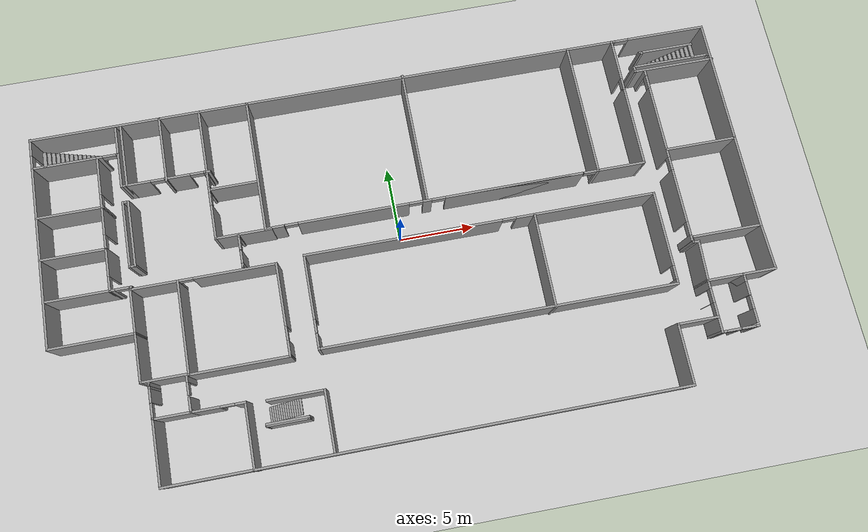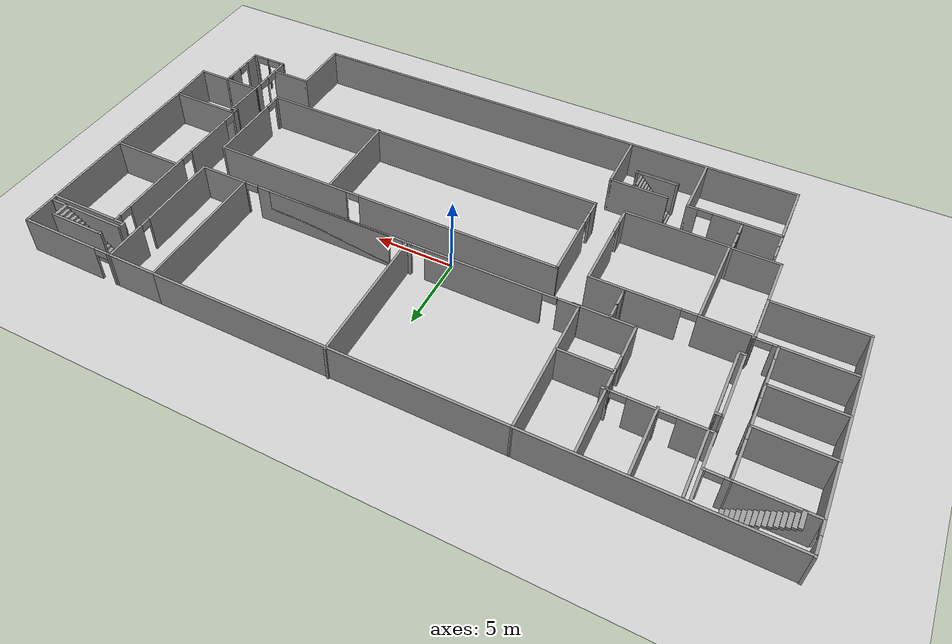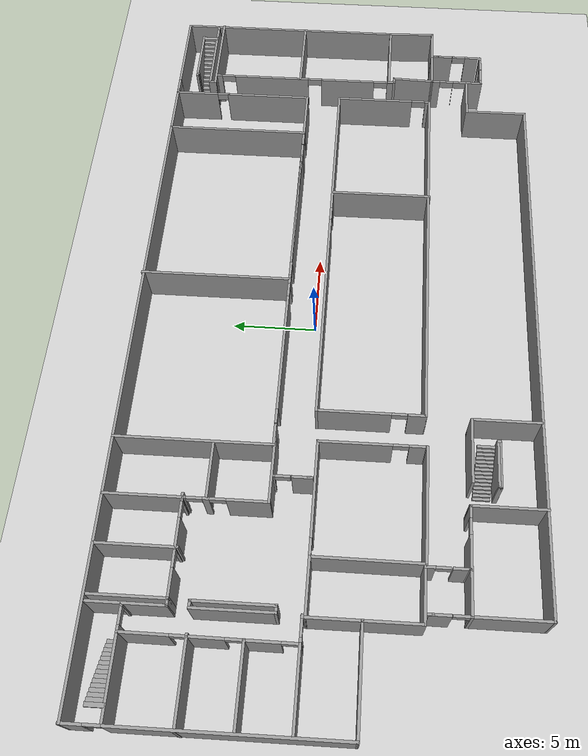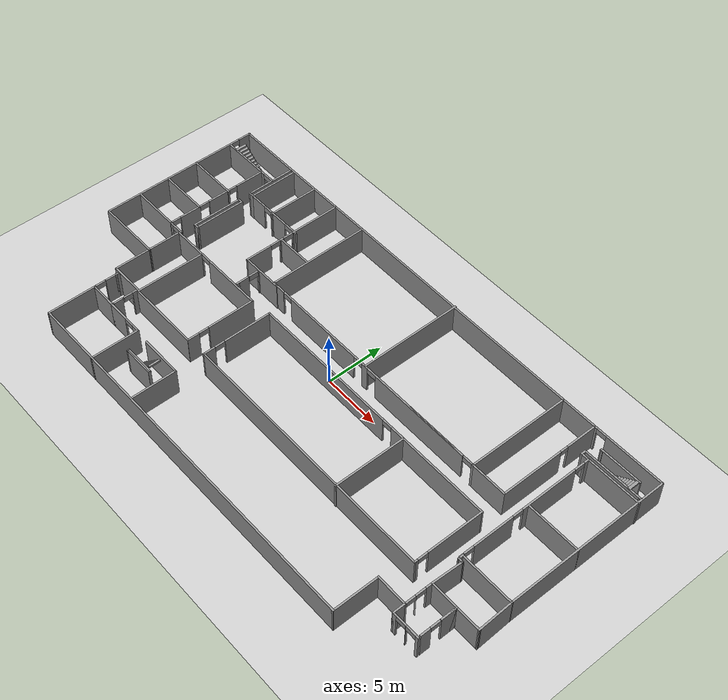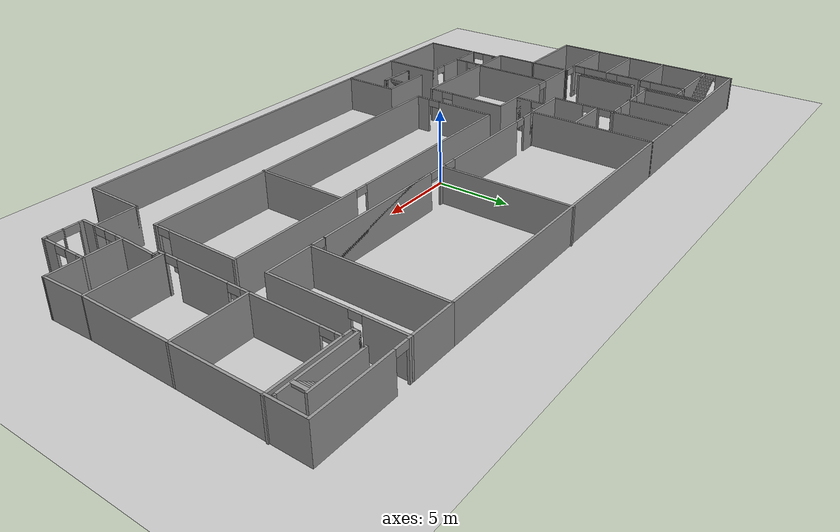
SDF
<sdf version="1.6">
 <world name="default">
  <light name="sun" type="directional">
   <pose>0 0 10 0 -0 0</pose>
   <diffuse>0.8 0.8 0.8 1</diffuse>
   <specular>0.1 0.1 0.1 1</specular>
   <attenuation>
    <range>1000</range>
    <constant>0.9</constant>
    <linear>0.01</linear>
    <quadratic>0.001</quadratic>
   </attenuation>
   <direction>-0.5 0.5 -1</direction>
  </light>
  <model name="ground_plane">
   <static>1</static>
   <link name="link">
    <collision name="collision">
     <geometry><plane><normal>0 0 1</normal><size>100 100</size></plane></geometry>
     <surface><friction><ode><mu>100</mu><mu2>50</mu2></ode></friction></surface>
    </collision>
    <visual name="visual">
     <cast_shadows>0</cast_shadows>
     <geometry><plane><normal>0 0 1</normal><size>100 100</size></plane></geometry>
     <material>
      <script><uri>file://media/materials/scripts/gazebo.material</uri><name>Gazebo/Grey</name></script>
     </material>
    </visual>
   </link>
  </model>
  <gravity>0 0 -9.8</gravity>
  <magnetic_field>6e-06 2.3e-05 -4.2e-05</magnetic_field>
  <atmosphere type="adiabatic"/>
  <physics name="default_physics" default="0" type="ode">
   <max_step_size>0.001</max_step_size>
   <real_time_factor>1</real_time_factor>
   <real_time_update_rate>1000</real_time_update_rate>
  </physics>
  <scene><ambient>0.4 0.4 0.4 1</ambient><background>0.7 0.7 0.7 1</background><shadows>1</shadows></scene>
  <spherical_coordinates>
   <surface_model>EARTH_WGS84</surface_model>
   <latitude_deg>0</latitude_deg>
   <longitude_deg>0</longitude_deg>
   <elevation>0</elevation>
   <heading_deg>0</heading_deg>
  </spherical_coordinates>
  <model name="Devon1_test">
   <pose>0.002437 -1.27806 0 0 -0 0</pose>
   <link name="Stairs_5">
    <visual name="Stairs_5_Visual_0">
     <pose>-10.1985 -8.6433 0.083333 0 -0 1.5708</pose>
     <geometry><box><size>1 0.155676 0.166667</size></box></geometry>
     <material>
      <script><uri>file://media/materials/scripts/gazebo.material</uri><name>Gazebo/Grey</name></script>
      <ambient>1 1 1 1</ambient>
     </material>
    </visual>
    <collision name="Stairs_5_Collision_0">
     <geometry><box><size>1 0.155676 0.166667</size></box></geometry>
     <pose>-10.1985 -8.6433 0.083333 0 -0 1.5708</pose>
    </collision>
    <visual name="Stairs_5_Visual_1">
     <pose>-10.0429 -8.6433 0.25 0 -0 1.5708</pose>
     <geometry><box><size>1 0.155676 0.166667</size></box></geometry>
     <material>
      <script><uri>file://media/materials/scripts/gazebo.material</uri><name>Gazebo/Grey</name></script>
      <ambient>1 1 1 1</ambient>
     </material>
    </visual>
    <collision name="Stairs_5_Collision_1">
     <geometry><box><size>1 0.155676 0.166667</size></box></geometry>
     <pose>-10.0429 -8.6433 0.25 0 -0 1.5708</pose>
    </collision>
    <visual name="Stairs_5_Visual_2">
     <pose>-9.88718 -8.6433 0.416667 0 -0 1.5708</pose>
     <geometry><box><size>1 0.155676 0.166667</size></box></geometry>
     <material>
      <script><uri>file://media/materials/scripts/gazebo.material</uri><name>Gazebo/Grey</name></script>
      <ambient>1 1 1 1</ambient>
     </material>
    </visual>
    <collision name="Stairs_5_Collision_2">
     <geometry><box><size>1 0.155676 0.166667</size></box></geometry>
     <pose>-9.88718 -8.6433 0.416667 0 -0 1.5708</pose>
    </collision>
    <visual name="Stairs_5_Visual_3">
     <pose>-9.7315 -8.6433 0.583333 0 -0 1.5708</pose>
     <geometry><box><size>1 0.155676 0.166667</size></box></geometry>
     <material>
      <script><uri>file://media/materials/scripts/gazebo.material</uri><name>Gazebo/Grey</name></script>
      <ambient>1 1 1 1</ambient>
     </material>
    </visual>
    <collision name="Stairs_5_Collision_3">
     <geometry><box><size>1 0.155676 0.166667</size></box></geometry>
     <pose>-9.7315 -8.6433 0.583333 0 -0 1.5708</pose>
    </collision>
    <visual name="Stairs_5_Visual_4">
     <pose>-9.57583 -8.6433 0.75 0 -0 1.5708</pose>
     <geometry><box><size>1 0.155676 0.166667</size></box></geometry>
     <material>
      <script><uri>file://media/materials/scripts/gazebo.material</uri><name>Gazebo/Grey</name></script>
      <ambient>1 1 1 1</ambient>
     </material>
    </visual>
    <collision name="Stairs_5_Collision_4">
     <geometry><box><size>1 0.155676 0.166667</size></box></geometry>
     <pose>-9.57583 -8.6433 0.75 0 -0 1.5708</pose>
    </collision>
    <visual name="Stairs_5_Visual_5">
     <pose>-9.42015 -8.6433 0.916667 0 -0 1.5708</pose>
     <geometry><box><size>1 0.155676 0.166667</size></box></geometry>
     <material>
      <script><uri>file://media/materials/scripts/gazebo.material</uri><name>Gazebo/Grey</name></script>
      <ambient>1 1 1 1</ambient>
     </material>
    </visual>
    <collision name="Stairs_5_Collision_5">
     <geometry><box><size>1 0.155676 0.166667</size></box></geometry>
     <pose>-9.42015 -8.6433 0.916667 0 -0 1.5708</pose>
    </collision>
    <visual name="Stairs_5_Visual_6">
     <pose>-9.26447 -8.6433 1.08333 0 -0 1.5708</pose>
     <geometry><box><size>1 0.155676 0.166667</size></box></geometry>
     <material>
      <script><uri>file://media/materials/scripts/gazebo.material</uri><name>Gazebo/Grey</name></script>
      <ambient>1 1 1 1</ambient>
     </material>
    </visual>
    <collision name="Stairs_5_Collision_6">
     <geometry><box><size>1 0.155676 0.166667</size></box></geometry>
     <pose>-9.26447 -8.6433 1.08333 0 -0 1.5708</pose>
    </collision>
    <visual name="Stairs_5_Visual_7">
     <pose>-9.1088 -8.6433 1.25 0 -0 1.5708</pose>
     <geometry><box><size>1 0.155676 0.166667</size></box></geometry>
     <material>
      <script><uri>file://media/materials/scripts/gazebo.material</uri><name>Gazebo/Grey</name></script>
      <ambient>1 1 1 1</ambient>
     </material>
    </visual>
    <collision name="Stairs_5_Collision_7">
     <geometry><box><size>1 0.155676 0.166667</size></box></geometry>
     <pose>-9.1088 -8.6433 1.25 0 -0 1.5708</pose>
    </collision>
    <visual name="Stairs_5_Visual_8">
     <pose>-8.95312 -8.6433 1.41667 0 -0 1.5708</pose>
     <geometry><box><size>1 0.155676 0.166667</size></box></geometry>
     <material>
      <script><uri>file://media/materials/scripts/gazebo.material</uri><name>Gazebo/Grey</name></script>
      <ambient>1 1 1 1</ambient>
     </material>
    </visual>
    <collision name="Stairs_5_Collision_8">
     <geometry><box><size>1 0.155676 0.166667</size></box></geometry>
     <pose>-8.95312 -8.6433 1.41667 0 -0 1.5708</pose>
    </collision>
    <visual name="Stairs_5_Visual_9">
     <pose>-8.79744 -8.6433 1.58333 0 -0 1.5708</pose>
     <geometry><box><size>1 0.155676 0.166667</size></box></geometry>
     <material>
      <script><uri>file://media/materials/scripts/gazebo.material</uri><name>Gazebo/Grey</name></script>
      <ambient>1 1 1 1</ambient>
     </material>
    </visual>
    <collision name="Stairs_5_Collision_9">
     <geometry><box><size>1 0.155676 0.166667</size></box></geometry>
     <pose>-8.79744 -8.6433 1.58333 0 -0 1.5708</pose>
    </collision>
    <visual name="Stairs_5_Visual_10">
     <pose>-8.64177 -8.6433 1.75 0 -0 1.5708</pose>
     <geometry><box><size>1 0.155676 0.166667</size></box></geometry>
     <material>
      <script><uri>file://media/materials/scripts/gazebo.material</uri><name>Gazebo/Grey</name></script>
      <ambient>1 1 1 1</ambient>
     </material>
    </visual>
    <collision name="Stairs_5_Collision_10">
     <geometry><box><size>1 0.155676 0.166667</size></box></geometry>
     <pose>-8.64177 -8.6433 1.75 0 -0 1.5708</pose>
    </collision>
    <visual name="Stairs_5_Visual_11">
     <pose>-8.48609 -8.6433 1.91667 0 -0 1.5708</pose>
     <geometry><box><size>1 0.155676 0.166667</size></box></geometry>
     <material>
      <script><uri>file://media/materials/scripts/gazebo.material</uri><name>Gazebo/Grey</name></script>
      <ambient>1 1 1 1</ambient>
     </material>
    </visual>
    <collision name="Stairs_5_Collision_11">
     <geometry><box><size>1 0.155676 0.166667</size></box></geometry>
     <pose>-8.48609 -8.6433 1.91667 0 -0 1.5708</pose>
    </collision>
    <visual name="Stairs_5_Visual_12">
     <pose>-8.33042 -8.6433 2.08333 0 -0 1.5708</pose>
     <geometry><box><size>1 0.155676 0.166667</size></box></geometry>
     <material>
      <script><uri>file://media/materials/scripts/gazebo.material</uri><name>Gazebo/Grey</name></script>
      <ambient>1 1 1 1</ambient>
     </material>
    </visual>
    <collision name="Stairs_5_Collision_12">
     <geometry><box><size>1 0.155676 0.166667</size></box></geometry>
     <pose>-8.33042 -8.6433 2.08333 0 -0 1.5708</pose>
    </collision>
    <visual name="Stairs_5_Visual_13">
     <pose>-8.17474 -8.6433 2.25 0 -0 1.5708</pose>
     <geometry><box><size>1 0.155676 0.166667</size></box></geometry>
     <material>
      <script><uri>file://media/materials/scripts/gazebo.material</uri><name>Gazebo/Grey</name></script>
      <ambient>1 1 1 1</ambient>
     </material>
    </visual>
    <collision name="Stairs_5_Collision_13">
     <geometry><box><size>1 0.155676 0.166667</size></box></geometry>
     <pose>-8.17474 -8.6433 2.25 0 -0 1.5708</pose>
    </collision>
    <visual name="Stairs_5_Visual_14">
     <pose>-8.01906 -8.6433 2.41667 0 -0 1.5708</pose>
     <geometry><box><size>1 0.155676 0.166667</size></box></geometry>
     <material>
      <script><uri>file://media/materials/scripts/gazebo.material</uri><name>Gazebo/Grey</name></script>
      <ambient>1 1 1 1</ambient>
     </material>
    </visual>
    <collision name="Stairs_5_Collision_14">
     <geometry><box><size>1 0.155676 0.166667</size></box></geometry>
     <pose>-8.01906 -8.6433 2.41667 0 -0 1.5708</pose>
    </collision>
   </link>
   <link name="Stairs_6">
    <visual name="Stairs_6_Visual_0">
     <pose>-18.9091 10.232 0.083333 0 -0 -1.5708</pose>
     <geometry><box><size>1 0.233333 0.166667</size></box></geometry>
     <material>
      <script><uri>file://media/materials/scripts/gazebo.material</uri><name>Gazebo/Grey</name></script>
      <ambient>1 1 1 1</ambient>
     </material>
    </visual>
    <collision name="Stairs_6_Collision_0">
     <geometry><box><size>1 0.233333 0.166667</size></box></geometry>
     <pose>-18.9091 10.232 0.083333 0 -0 -1.5708</pose>
    </collision>
    <visual name="Stairs_6_Visual_1">
     <pose>-19.1424 10.232 0.25 0 -0 -1.5708</pose>
     <geometry><box><size>1 0.233333 0.166667</size></box></geometry>
     <material>
      <script><uri>file://media/materials/scripts/gazebo.material</uri><name>Gazebo/Grey</name></script>
      <ambient>1 1 1 1</ambient>
     </material>
    </visual>
    <collision name="Stairs_6_Collision_1">
     <geometry><box><size>1 0.233333 0.166667</size></box></geometry>
     <pose>-19.1424 10.232 0.25 0 -0 -1.5708</pose>
    </collision>
    <visual name="Stairs_6_Visual_2">
     <pose>-19.3758 10.232 0.416667 0 -0 -1.5708</pose>
     <geometry><box><size>1 0.233333 0.166667</size></box></geometry>
     <material>
      <script><uri>file://media/materials/scripts/gazebo.material</uri><name>Gazebo/Grey</name></script>
      <ambient>1 1 1 1</ambient>
     </material>
    </visual>
    <collision name="Stairs_6_Collision_2">
     <geometry><box><size>1 0.233333 0.166667</size></box></geometry>
     <pose>-19.3758 10.232 0.416667 0 -0 -1.5708</pose>
    </collision>
    <visual name="Stairs_6_Visual_3">
     <pose>-19.6091 10.232 0.583333 0 -0 -1.5708</pose>
     <geometry><box><size>1 0.233333 0.166667</size></box></geometry>
     <material>
      <script><uri>file://media/materials/scripts/gazebo.material</uri><name>Gazebo/Grey</name></script>
      <ambient>1 1 1 1</ambient>
     </material>
    </visual>
    <collision name="Stairs_6_Collision_3">
     <geometry><box><size>1 0.233333 0.166667</size></box></geometry>
     <pose>-19.6091 10.232 0.583333 0 -0 -1.5708</pose>
    </collision>
    <visual name="Stairs_6_Visual_4">
     <pose>-19.8424 10.232 0.75 0 -0 -1.5708</pose>
     <geometry><box><size>1 0.233333 0.166667</size></box></geometry>
     <material>
      <script><uri>file://media/materials/scripts/gazebo.material</uri><name>Gazebo/Grey</name></script>
      <ambient>1 1 1 1</ambient>
     </material>
    </visual>
    <collision name="Stairs_6_Collision_4">
     <geometry><box><size>1 0.233333 0.166667</size></box></geometry>
     <pose>-19.8424 10.232 0.75 0 -0 -1.5708</pose>
    </collision>
    <visual name="Stairs_6_Visual_5">
     <pose>-20.0757 10.232 0.916667 0 -0 -1.5708</pose>
     <geometry><box><size>1 0.233333 0.166667</size></box></geometry>
     <material>
      <script><uri>file://media/materials/scripts/gazebo.material</uri><name>Gazebo/Grey</name></script>
      <ambient>1 1 1 1</ambient>
     </material>
    </visual>
    <collision name="Stairs_6_Collision_5">
     <geometry><box><size>1 0.233333 0.166667</size></box></geometry>
     <pose>-20.0757 10.232 0.916667 0 -0 -1.5708</pose>
    </collision>
    <visual name="Stairs_6_Visual_6">
     <pose>-20.3091 10.232 1.08333 0 -0 -1.5708</pose>
     <geometry><box><size>1 0.233333 0.166667</size></box></geometry>
     <material>
      <script><uri>file://media/materials/scripts/gazebo.material</uri><name>Gazebo/Grey</name></script>
      <ambient>1 1 1 1</ambient>
     </material>
    </visual>
    <collision name="Stairs_6_Collision_6">
     <geometry><box><size>1 0.233333 0.166667</size></box></geometry>
     <pose>-20.3091 10.232 1.08333 0 -0 -1.5708</pose>
    </collision>
    <visual name="Stairs_6_Visual_7">
     <pose>-20.5424 10.232 1.25 0 -0 -1.5708</pose>
     <geometry><box><size>1 0.233333 0.166667</size></box></geometry>
     <material>
      <script><uri>file://media/materials/scripts/gazebo.material</uri><name>Gazebo/Grey</name></script>
      <ambient>1 1 1 1</ambient>
     </material>
    </visual>
    <collision name="Stairs_6_Collision_7">
     <geometry><box><size>1 0.233333 0.166667</size></box></geometry>
     <pose>-20.5424 10.232 1.25 0 -0 -1.5708</pose>
    </collision>
    <visual name="Stairs_6_Visual_8">
     <pose>-20.7757 10.232 1.41667 0 -0 -1.5708</pose>
     <geometry><box><size>1 0.233333 0.166667</size></box></geometry>
     <material>
      <script><uri>file://media/materials/scripts/gazebo.material</uri><name>Gazebo/Grey</name></script>
      <ambient>1 1 1 1</ambient>
     </material>
    </visual>
    <collision name="Stairs_6_Collision_8">
     <geometry><box><size>1 0.233333 0.166667</size></box></geometry>
     <pose>-20.7757 10.232 1.41667 0 -0 -1.5708</pose>
    </collision>
    <visual name="Stairs_6_Visual_9">
     <pose>-21.0091 10.232 1.58333 0 -0 -1.5708</pose>
     <geometry><box><size>1 0.233333 0.166667</size></box></geometry>
     <material>
      <script><uri>file://media/materials/scripts/gazebo.material</uri><name>Gazebo/Grey</name></script>
      <ambient>1 1 1 1</ambient>
     </material>
    </visual>
    <collision name="Stairs_6_Collision_9">
     <geometry><box><size>1 0.233333 0.166667</size></box></geometry>
     <pose>-21.0091 10.232 1.58333 0 -0 -1.5708</pose>
    </collision>
    <visual name="Stairs_6_Visual_10">
     <pose>-21.2424 10.232 1.75 0 -0 -1.5708</pose>
     <geometry><box><size>1 0.233333 0.166667</size></box></geometry>
     <material>
      <script><uri>file://media/materials/scripts/gazebo.material</uri><name>Gazebo/Grey</name></script>
      <ambient>1 1 1 1</ambient>
     </material>
    </visual>
    <collision name="Stairs_6_Collision_10">
     <geometry><box><size>1 0.233333 0.166667</size></box></geometry>
     <pose>-21.2424 10.232 1.75 0 -0 -1.5708</pose>
    </collision>
    <visual name="Stairs_6_Visual_11">
     <pose>-21.4758 10.232 1.91667 0 -0 -1.5708</pose>
     <geometry><box><size>1 0.233333 0.166667</size></box></geometry>
     <material>
      <script><uri>file://media/materials/scripts/gazebo.material</uri><name>Gazebo/Grey</name></script>
      <ambient>1 1 1 1</ambient>
     </material>
    </visual>
    <collision name="Stairs_6_Collision_11">
     <geometry><box><size>1 0.233333 0.166667</size></box></geometry>
     <pose>-21.4758 10.232 1.91667 0 -0 -1.5708</pose>
    </collision>
    <visual name="Stairs_6_Visual_12">
     <pose>-21.7091 10.232 2.08333 0 -0 -1.5708</pose>
     <geometry><box><size>1 0.233333 0.166667</size></box></geometry>
     <material>
      <script><uri>file://media/materials/scripts/gazebo.material</uri><name>Gazebo/Grey</name></script>
      <ambient>1 1 1 1</ambient>
     </material>
    </visual>
    <collision name="Stairs_6_Collision_12">
     <geometry><box><size>1 0.233333 0.166667</size></box></geometry>
     <pose>-21.7091 10.232 2.08333 0 -0 -1.5708</pose>
    </collision>
    <visual name="Stairs_6_Visual_13">
     <pose>-21.9424 10.232 2.25 0 -0 -1.5708</pose>
     <geometry><box><size>1 0.233333 0.166667</size></box></geometry>
     <material>
      <script><uri>file://media/materials/scripts/gazebo.material</uri><name>Gazebo/Grey</name></script>
      <ambient>1 1 1 1</ambient>
     </material>
    </visual>
    <collision name="Stairs_6_Collision_13">
     <geometry><box><size>1 0.233333 0.166667</size></box></geometry>
     <pose>-21.9424 10.232 2.25 0 -0 -1.5708</pose>
    </collision>
    <visual name="Stairs_6_Visual_14">
     <pose>-22.1757 10.232 2.41667 0 -0 -1.5708</pose>
     <geometry><box><size>1 0.233333 0.166667</size></box></geometry>
     <material>
      <script><uri>file://media/materials/scripts/gazebo.material</uri><name>Gazebo/Grey</name></script>
      <ambient>1 1 1 1</ambient>
     </material>
    </visual>
    <collision name="Stairs_6_Collision_14">
     <geometry><box><size>1 0.233333 0.166667</size></box></geometry>
     <pose>-22.1757 10.232 2.41667 0 -0 -1.5708</pose>
    </collision>
   </link>
   <link name="Stairs_8">
    <visual name="Stairs_8_Visual_0">
     <pose>18.5359 10.1599 0.083333 0 -0 1.5708</pose>
     <geometry><box><size>0.910609 0.233333 0.166667</size></box></geometry>
     <material>
      <script><uri>file://media/materials/scripts/gazebo.material</uri><name>Gazebo/Grey</name></script>
      <ambient>1 1 1 1</ambient>
     </material>
    </visual>
    <collision name="Stairs_8_Collision_0">
     <geometry><box><size>0.910609 0.233333 0.166667</size></box></geometry>
     <pose>18.5359 10.1599 0.083333 0 -0 1.5708</pose>
    </collision>
    <visual name="Stairs_8_Visual_1">
     <pose>18.7693 10.1599 0.25 0 -0 1.5708</pose>
     <geometry><box><size>0.910609 0.233333 0.166667</size></box></geometry>
     <material>
      <script><uri>file://media/materials/scripts/gazebo.material</uri><name>Gazebo/Grey</name></script>
      <ambient>1 1 1 1</ambient>
     </material>
    </visual>
    <collision name="Stairs_8_Collision_1">
     <geometry><box><size>0.910609 0.233333 0.166667</size></box></geometry>
     <pose>18.7693 10.1599 0.25 0 -0 1.5708</pose>
    </collision>
    <visual name="Stairs_8_Visual_2">
     <pose>19.0026 10.1599 0.416667 0 -0 1.5708</pose>
     <geometry><box><size>0.910609 0.233333 0.166667</size></box></geometry>
     <material>
      <script><uri>file://media/materials/scripts/gazebo.material</uri><name>Gazebo/Grey</name></script>
      <ambient>1 1 1 1</ambient>
     </material>
    </visual>
    <collision name="Stairs_8_Collision_2">
     <geometry><box><size>0.910609 0.233333 0.166667</size></box></geometry>
     <pose>19.0026 10.1599 0.416667 0 -0 1.5708</pose>
    </collision>
    <visual name="Stairs_8_Visual_3">
     <pose>19.2359 10.1599 0.583333 0 -0 1.5708</pose>
     <geometry><box><size>0.910609 0.233333 0.166667</size></box></geometry>
     <material>
      <script><uri>file://media/materials/scripts/gazebo.material</uri><name>Gazebo/Grey</name></script>
      <ambient>1 1 1 1</ambient>
     </material>
    </visual>
    <collision name="Stairs_8_Collision_3">
     <geometry><box><size>0.910609 0.233333 0.166667</size></box></geometry>
     <pose>19.2359 10.1599 0.583333 0 -0 1.5708</pose>
    </collision>
    <visual name="Stairs_8_Visual_4">
     <pose>19.4693 10.1599 0.75 0 -0 1.5708</pose>
     <geometry><box><size>0.910609 0.233333 0.166667</size></box></geometry>
     <material>
      <script><uri>file://media/materials/scripts/gazebo.material</uri><name>Gazebo/Grey</name></script>
      <ambient>1 1 1 1</ambient>
     </material>
    </visual>
    <collision name="Stairs_8_Collision_4">
     <geometry><box><size>0.910609 0.233333 0.166667</size></box></geometry>
     <pose>19.4693 10.1599 0.75 0 -0 1.5708</pose>
    </collision>
    <visual name="Stairs_8_Visual_5">
     <pose>19.7026 10.1599 0.916667 0 -0 1.5708</pose>
     <geometry><box><size>0.910609 0.233333 0.166667</size></box></geometry>
     <material>
      <script><uri>file://media/materials/scripts/gazebo.material</uri><name>Gazebo/Grey</name></script>
      <ambient>1 1 1 1</ambient>
     </material>
    </visual>
    <collision name="Stairs_8_Collision_5">
     <geometry><box><size>0.910609 0.233333 0.166667</size></box></geometry>
     <pose>19.7026 10.1599 0.916667 0 -0 1.5708</pose>
    </collision>
    <visual name="Stairs_8_Visual_6">
     <pose>19.9359 10.1599 1.08333 0 -0 1.5708</pose>
     <geometry><box><size>0.910609 0.233333 0.166667</size></box></geometry>
     <material>
      <script><uri>file://media/materials/scripts/gazebo.material</uri><name>Gazebo/Grey</name></script>
      <ambient>1 1 1 1</ambient>
     </material>
    </visual>
    <collision name="Stairs_8_Collision_6">
     <geometry><box><size>0.910609 0.233333 0.166667</size></box></geometry>
     <pose>19.9359 10.1599 1.08333 0 -0 1.5708</pose>
    </collision>
    <visual name="Stairs_8_Visual_7">
     <pose>20.1693 10.1599 1.25 0 -0 1.5708</pose>
     <geometry><box><size>0.910609 0.233333 0.166667</size></box></geometry>
     <material>
      <script><uri>file://media/materials/scripts/gazebo.material</uri><name>Gazebo/Grey</name></script>
      <ambient>1 1 1 1</ambient>
     </material>
    </visual>
    <collision name="Stairs_8_Collision_7">
     <geometry><box><size>0.910609 0.233333 0.166667</size></box></geometry>
     <pose>20.1693 10.1599 1.25 0 -0 1.5708</pose>
    </collision>
    <visual name="Stairs_8_Visual_8">
     <pose>20.4026 10.1599 1.41667 0 -0 1.5708</pose>
     <geometry><box><size>0.910609 0.233333 0.166667</size></box></geometry>
     <material>
      <script><uri>file://media/materials/scripts/gazebo.material</uri><name>Gazebo/Grey</name></script>
      <ambient>1 1 1 1</ambient>
     </material>
    </visual>
    <collision name="Stairs_8_Collision_8">
     <geometry><box><size>0.910609 0.233333 0.166667</size></box></geometry>
     <pose>20.4026 10.1599 1.41667 0 -0 1.5708</pose>
    </collision>
    <visual name="Stairs_8_Visual_9">
     <pose>20.6359 10.1599 1.58333 0 -0 1.5708</pose>
     <geometry><box><size>0.910609 0.233333 0.166667</size></box></geometry>
     <material>
      <script><uri>file://media/materials/scripts/gazebo.material</uri><name>Gazebo/Grey</name></script>
      <ambient>1 1 1 1</ambient>
     </material>
    </visual>
    <collision name="Stairs_8_Collision_9">
     <geometry><box><size>0.910609 0.233333 0.166667</size></box></geometry>
     <pose>20.6359 10.1599 1.58333 0 -0 1.5708</pose>
    </collision>
    <visual name="Stairs_8_Visual_10">
     <pose>20.8693 10.1599 1.75 0 -0 1.5708</pose>
     <geometry><box><size>0.910609 0.233333 0.166667</size></box></geometry>
     <material>
      <script><uri>file://media/materials/scripts/gazebo.material</uri><name>Gazebo/Grey</name></script>
      <ambient>1 1 1 1</ambient>
     </material>
    </visual>
    <collision name="Stairs_8_Collision_10">
     <geometry><box><size>0.910609 0.233333 0.166667</size></box></geometry>
     <pose>20.8693 10.1599 1.75 0 -0 1.5708</pose>
    </collision>
    <visual name="Stairs_8_Visual_11">
     <pose>21.1026 10.1599 1.91667 0 -0 1.5708</pose>
     <geometry><box><size>0.910609 0.233333 0.166667</size></box></geometry>
     <material>
      <script><uri>file://media/materials/scripts/gazebo.material</uri><name>Gazebo/Grey</name></script>
      <ambient>1 1 1 1</ambient>
     </material>
    </visual>
    <collision name="Stairs_8_Collision_11">
     <geometry><box><size>0.910609 0.233333 0.166667</size></box></geometry>
     <pose>21.1026 10.1599 1.91667 0 -0 1.5708</pose>
    </collision>
    <visual name="Stairs_8_Visual_12">
     <pose>21.3359 10.1599 2.08333 0 -0 1.5708</pose>
     <geometry><box><size>0.910609 0.233333 0.166667</size></box></geometry>
     <material>
      <script><uri>file://media/materials/scripts/gazebo.material</uri><name>Gazebo/Grey</name></script>
      <ambient>1 1 1 1</ambient>
     </material>
    </visual>
    <collision name="Stairs_8_Collision_12">
     <geometry><box><size>0.910609 0.233333 0.166667</size></box></geometry>
     <pose>21.3359 10.1599 2.08333 0 -0 1.5708</pose>
    </collision>
    <visual name="Stairs_8_Visual_13">
     <pose>21.5693 10.1599 2.25 0 -0 1.5708</pose>
     <geometry><box><size>0.910609 0.233333 0.166667</size></box></geometry>
     <material>
      <script><uri>file://media/materials/scripts/gazebo.material</uri><name>Gazebo/Grey</name></script>
      <ambient>1 1 1 1</ambient>
     </material>
    </visual>
    <collision name="Stairs_8_Collision_13">
     <geometry><box><size>0.910609 0.233333 0.166667</size></box></geometry>
     <pose>21.5693 10.1599 2.25 0 -0 1.5708</pose>
    </collision>
    <visual name="Stairs_8_Visual_14">
     <pose>21.8026 10.1599 2.41667 0 -0 1.5708</pose>
     <geometry><box><size>0.910609 0.233333 0.166667</size></box></geometry>
     <material>
      <script><uri>file://media/materials/scripts/gazebo.material</uri><name>Gazebo/Grey</name></script>
      <ambient>1 1 1 1</ambient>
     </material>
    </visual>
    <collision name="Stairs_8_Collision_14">
     <geometry><box><size>0.910609 0.233333 0.166667</size></box></geometry>
     <pose>21.8026 10.1599 2.41667 0 -0 1.5708</pose>
    </collision>
   </link>
   <link name="Wall_0">
    <collision name="Wall_0_Collision">
     <geometry><box><size>9 0.15 2.5</size></box></geometry>
     <pose>0 0 1.25 0 -0 0</pose>
    </collision>
    <visual name="Wall_0_Visual">
     <pose>0 0 1.25 0 -0 0</pose>
     <geometry><box><size>9 0.15 2.5</size></box></geometry>
     <material>
      <script><uri>file://media/materials/scripts/gazebo.material</uri><name>Gazebo/Grey</name></script>
      <ambient>1 1 1 1</ambient>
     </material>
    </visual>
    <pose>13.5343 7.35639 0 0 0 -1.5708</pose>
   </link>
   <link name="Wall_1">
    <collision name="Wall_1_Collision">
     <geometry><box><size>3.25 0.15 2.5</size></box></geometry>
     <pose>0 0 1.25 0 -0 0</pose>
    </collision>
    <visual name="Wall_1_Visual">
     <pose>0 0 1.25 0 -0 0</pose>
     <geometry><box><size>3.25 0.15 2.5</size></box></geometry>
     <material>
      <script><uri>file://media/materials/scripts/gazebo.material</uri><name>Gazebo/Grey</name></script>
      <ambient>1 1 1 1</ambient>
     </material>
    </visual>
    <pose>15.0843 2.93139 0 0 -0 0</pose>
   </link>
   <link name="Wall_103">
    <collision name="Wall_103_Collision">
     <geometry><box><size>2.25 0.15 2.5</size></box></geometry>
     <pose>0 0 1.25 0 -0 0</pose>
    </collision>
    <visual name="Wall_103_Visual">
     <pose>0 0 1.25 0 -0 0</pose>
     <geometry><box><size>2.25 0.15 2.5</size></box></geometry>
     <material>
      <script><uri>file://media/materials/scripts/gazebo.material</uri><name>Gazebo/Grey</name></script>
      <ambient>1 1 1 1</ambient>
     </material>
    </visual>
    <pose>22.0343 -5.51861 0 0 -0 0</pose>
   </link>
   <link name="Wall_104">
    <collision name="Wall_104_Collision">
     <geometry><box><size>3.10169 0.15 2.5</size></box></geometry>
     <pose>0 0 1.25 0 -0 0</pose>
    </collision>
    <visual name="Wall_104_Visual">
     <pose>0 0 1.25 0 -0 0</pose>
     <geometry><box><size>3.10169 0.15 2.5</size></box></geometry>
     <material>
      <script><uri>file://media/materials/scripts/gazebo.material</uri><name>Gazebo/Grey</name></script>
      <ambient>1 1 1 1</ambient>
     </material>
    </visual>
    <pose>23.0343 -4.04361 0 0 -0 1.60468</pose>
   </link>
   <link name="Wall_106">
    <collision name="Wall_106_Collision">
     <geometry><box><size>0.5 0.15 2.5</size></box></geometry>
     <pose>0 0 1.25 0 -0 0</pose>
    </collision>
    <visual name="Wall_106_Visual">
     <pose>0 0 1.25 0 -0 0</pose>
     <geometry><box><size>0.5 0.15 2.5</size></box></geometry>
     <material>
      <script><uri>file://media/materials/scripts/gazebo.material</uri><name>Gazebo/Grey</name></script>
      <ambient>1 1 1 1</ambient>
     </material>
    </visual>
    <pose>18.3843 -2.74361 0 0 0 -1.5708</pose>
   </link>
   <link name="Wall_107">
    <collision name="Wall_107_Collision">
     <geometry><box><size>0.5 0.15 2.5</size></box></geometry>
     <pose>0 0 1.25 0 -0 0</pose>
    </collision>
    <visual name="Wall_107_Visual">
     <pose>0 0 1.25 0 -0 0</pose>
     <geometry><box><size>0.5 0.15 2.5</size></box></geometry>
     <material>
      <script><uri>file://media/materials/scripts/gazebo.material</uri><name>Gazebo/Grey</name></script>
      <ambient>1 1 1 1</ambient>
     </material>
    </visual>
    <pose>18.5593 -2.91861 0 0 -0 0</pose>
   </link>
   <link name="Wall_108">
    <collision name="Wall_108_Collision">
     <geometry><box><size>2.75192 0.15 2.5</size></box></geometry>
     <pose>0 0 1.25 0 -0 0</pose>
    </collision>
    <visual name="Wall_108_Visual">
     <pose>0 0 1.25 0 -0 0</pose>
     <geometry><box><size>2.75192 0.15 2.5</size></box></geometry>
     <material>
      <script><uri>file://media/materials/scripts/gazebo.material</uri><name>Gazebo/Grey</name></script>
      <ambient>1 1 1 1</ambient>
     </material>
    </visual>
    <pose>18.6843 -4.21861 0 0 0 -1.60924</pose>
   </link>
   <link name="Wall_11">
    <pose>19.8093 11.7814 0 0 -0 0</pose>
    <visual name="Wall_11_Visual_0">
     <pose>-3.09331 0 1.25 0 -0 0</pose>
     <geometry><box><size>0.31338 0.15 2.5</size></box></geometry>
     <material>
      <script><uri>file://media/materials/scripts/gazebo.material</uri><name>Gazebo/Grey</name></script>
      <ambient>1 1 1 1</ambient>
     </material>
    </visual>
    <collision name="Wall_11_Collision_0">
     <geometry><box><size>0.31338 0.15 2.5</size></box></geometry>
     <pose>-3.09331 0 1.25 0 -0 0</pose>
    </collision>
    <visual name="Wall_11_Visual_1">
     <pose>0.60669 0 1.25 0 -0 0</pose>
     <geometry><box><size>5.28662 0.15 2.5</size></box></geometry>
     <material>
      <script><uri>file://media/materials/scripts/gazebo.material</uri><name>Gazebo/Grey</name></script>
      <ambient>1 1 1 1</ambient>
     </material>
    </visual>
    <collision name="Wall_11_Collision_1">
     <geometry><box><size>5.28662 0.15 2.5</size></box></geometry>
     <pose>0.60669 0 1.25 0 -0 0</pose>
    </collision>
    <visual name="Wall_11_Visual_2">
     <pose>-2.48662 0 2.25 0 -0 0</pose>
     <geometry><box><size>0.9 0.15 0.5</size></box></geometry>
     <material>
      <script><uri>file://media/materials/scripts/gazebo.material</uri><name>Gazebo/Grey</name></script>
      <ambient>1 1 1 1</ambient>
     </material>
    </visual>
    <collision name="Wall_11_Collision_2">
     <geometry><box><size>0.9 0.15 0.5</size></box></geometry>
     <pose>-2.48662 0 2.25 0 -0 0</pose>
    </collision>
   </link>
   <link name="Wall_110">
    <pose>-6.38448 -2.30326 0 0 0 -1.5708</pose>
    <visual name="Wall_110_Visual_0">
     <pose>-0.987121 0 1.25 0 -0 0</pose>
     <geometry><box><size>4.27576 0.15 2.5</size></box></geometry>
     <material>
      <script><uri>file://media/materials/scripts/gazebo.material</uri><name>Gazebo/Grey</name></script>
      <ambient>1 1 1 1</ambient>
     </material>
    </visual>
    <collision name="Wall_110_Collision_0">
     <geometry><box><size>4.27576 0.15 2.5</size></box></geometry>
     <pose>-0.987121 0 1.25 0 -0 0</pose>
    </collision>
    <visual name="Wall_110_Visual_1">
     <pose>2.58788 0 1.25 0 -0 0</pose>
     <geometry><box><size>1.07424 0.15 2.5</size></box></geometry>
     <material>
      <script><uri>file://media/materials/scripts/gazebo.material</uri><name>Gazebo/Grey</name></script>
      <ambient>1 1 1 1</ambient>
     </material>
    </visual>
    <collision name="Wall_110_Collision_1">
     <geometry><box><size>1.07424 0.15 2.5</size></box></geometry>
     <pose>2.58788 0 1.25 0 -0 0</pose>
    </collision>
    <visual name="Wall_110_Visual_2">
     <pose>3.03392 0 1.25 0 -0 0</pose>
     <geometry><box><size>0.182154 0.15 2.5</size></box></geometry>
     <material>
      <script><uri>file://media/materials/scripts/gazebo.material</uri><name>Gazebo/Grey</name></script>
      <ambient>1 1 1 1</ambient>
     </material>
    </visual>
    <collision name="Wall_110_Collision_2">
     <geometry><box><size>0.182154 0.15 2.5</size></box></geometry>
     <pose>3.03392 0 1.25 0 -0 0</pose>
    </collision>
    <visual name="Wall_110_Visual_3">
     <pose>1.5968 0 2.25 0 -0 0</pose>
     <geometry><box><size>0.892089 0.15 0.5</size></box></geometry>
     <material>
      <script><uri>file://media/materials/scripts/gazebo.material</uri><name>Gazebo/Grey</name></script>
      <ambient>1 1 1 1</ambient>
     </material>
    </visual>
    <collision name="Wall_110_Collision_3">
     <geometry><box><size>0.892089 0.15 0.5</size></box></geometry>
     <pose>1.5968 0 2.25 0 -0 0</pose>
    </collision>
   </link>
   <link name="Wall_111">
    <collision name="Wall_111_Collision">
     <geometry><box><size>23.25 0.15 2.5</size></box></geometry>
     <pose>0 0 1.25 0 -0 0</pose>
    </collision>
    <visual name="Wall_111_Visual">
     <pose>0 0 1.25 0 -0 0</pose>
     <geometry><box><size>23.25 0.15 2.5</size></box></geometry>
     <material>
      <script><uri>file://media/materials/scripts/gazebo.material</uri><name>Gazebo/Grey</name></script>
      <ambient>1 1 1 1</ambient>
     </material>
    </visual>
    <pose>5.16552 -5.35326 0 0 -0 0</pose>
   </link>
   <link name="Wall_112">
    <pose>16.7155 -2.30326 0 0 -0 1.5708</pose>
    <visual name="Wall_112_Visual_0">
     <pose>-2.94471 0 1.25 0 -0 0</pose>
     <geometry><box><size>0.360572 0.15 2.5</size></box></geometry>
     <material>
      <script><uri>file://media/materials/scripts/gazebo.material</uri><name>Gazebo/Grey</name></script>
      <ambient>1 1 1 1</ambient>
     </material>
    </visual>
    <collision name="Wall_112_Collision_0">
     <geometry><box><size>0.360572 0.15 2.5</size></box></geometry>
     <pose>-2.94471 0 1.25 0 -0 0</pose>
    </collision>
    <visual name="Wall_112_Visual_1">
     <pose>0.630286 0 1.25 0 -0 0</pose>
     <geometry><box><size>4.98943 0.15 2.5</size></box></geometry>
     <material>
      <script><uri>file://media/materials/scripts/gazebo.material</uri><name>Gazebo/Grey</name></script>
      <ambient>1 1 1 1</ambient>
     </material>
    </visual>
    <collision name="Wall_112_Collision_1">
     <geometry><box><size>4.98943 0.15 2.5</size></box></geometry>
     <pose>0.630286 0 1.25 0 -0 0</pose>
    </collision>
    <visual name="Wall_112_Visual_2">
     <pose>-2.31443 0 2.25 0 -0 0</pose>
     <geometry><box><size>0.9 0.15 0.5</size></box></geometry>
     <material>
      <script><uri>file://media/materials/scripts/gazebo.material</uri><name>Gazebo/Grey</name></script>
      <ambient>1 1 1 1</ambient>
     </material>
    </visual>
    <collision name="Wall_112_Collision_2">
     <geometry><box><size>0.9 0.15 0.5</size></box></geometry>
     <pose>-2.31443 0 2.25 0 -0 0</pose>
    </collision>
   </link>
   <link name="Wall_113">
    <pose>5.16552 0.74674 0 0 -0 3.14159</pose>
    <visual name="Wall_113_Visual_0">
     <pose>-6.98964 0 1.25 0 -0 0</pose>
     <geometry><box><size>9.27072 0.15 2.5</size></box></geometry>
     <material>
      <script><uri>file://media/materials/scripts/gazebo.material</uri><name>Gazebo/Grey</name></script>
      <ambient>1 1 1 1</ambient>
     </material>
    </visual>
    <collision name="Wall_113_Collision_0">
     <geometry><box><size>9.27072 0.15 2.5</size></box></geometry>
     <pose>-6.98964 0 1.25 0 -0 0</pose>
    </collision>
    <visual name="Wall_113_Visual_1">
     <pose>5.08536 0 1.25 0 -0 0</pose>
     <geometry><box><size>13.0793 0.15 2.5</size></box></geometry>
     <material>
      <script><uri>file://media/materials/scripts/gazebo.material</uri><name>Gazebo/Grey</name></script>
      <ambient>1 1 1 1</ambient>
     </material>
    </visual>
    <collision name="Wall_113_Collision_1">
     <geometry><box><size>13.0793 0.15 2.5</size></box></geometry>
     <pose>5.08536 0 1.25 0 -0 0</pose>
    </collision>
    <visual name="Wall_113_Visual_2">
     <pose>-1.90428 0 2.25 0 -0 0</pose>
     <geometry><box><size>0.9 0.15 0.5</size></box></geometry>
     <material>
      <script><uri>file://media/materials/scripts/gazebo.material</uri><name>Gazebo/Grey</name></script>
      <ambient>1 1 1 1</ambient>
     </material>
    </visual>
    <collision name="Wall_113_Collision_2">
     <geometry><box><size>0.9 0.15 0.5</size></box></geometry>
     <pose>-1.90428 0 2.25 0 -0 0</pose>
    </collision>
   </link>
   <link name="Wall_115">
    <collision name="Wall_115_Collision">
     <geometry><box><size>6.25 0.15 2.5</size></box></geometry>
     <pose>0 0 1.25 0 -0 0</pose>
    </collision>
    <visual name="Wall_115_Visual">
     <pose>0 0 1.25 0 -0 0</pose>
     <geometry><box><size>6.25 0.15 2.5</size></box></geometry>
     <material>
      <script><uri>file://media/materials/scripts/gazebo.material</uri><name>Gazebo/Grey</name></script>
      <ambient>1 1 1 1</ambient>
     </material>
    </visual>
    <pose>8.74958 -2.37463 0 0 0 -1.5708</pose>
   </link>
   <link name="Wall_117">
    <pose>-13.0407 -7.76861 0 0 -0 0</pose>
    <visual name="Wall_117_Visual_0">
     <pose>-0.810078 0 1.25 0 -0 0</pose>
     <geometry><box><size>1.87984 0.15 2.5</size></box></geometry>
     <material>
      <script><uri>file://media/materials/scripts/gazebo.material</uri><name>Gazebo/Grey</name></script>
      <ambient>1 1 1 1</ambient>
     </material>
    </visual>
    <collision name="Wall_117_Collision_0">
     <geometry><box><size>1.87984 0.15 2.5</size></box></geometry>
     <pose>-0.810078 0 1.25 0 -0 0</pose>
    </collision>
    <visual name="Wall_117_Visual_1">
     <pose>1.38992 0 1.25 0 -0 0</pose>
     <geometry><box><size>0.720156 0.15 2.5</size></box></geometry>
     <material>
      <script><uri>file://media/materials/scripts/gazebo.material</uri><name>Gazebo/Grey</name></script>
      <ambient>1 1 1 1</ambient>
     </material>
    </visual>
    <collision name="Wall_117_Collision_1">
     <geometry><box><size>0.720156 0.15 2.5</size></box></geometry>
     <pose>1.38992 0 1.25 0 -0 0</pose>
    </collision>
    <visual name="Wall_117_Visual_2">
     <pose>0.579844 0 2.25 0 -0 0</pose>
     <geometry><box><size>0.9 0.15 0.5</size></box></geometry>
     <material>
      <script><uri>file://media/materials/scripts/gazebo.material</uri><name>Gazebo/Grey</name></script>
      <ambient>1 1 1 1</ambient>
     </material>
    </visual>
    <collision name="Wall_117_Collision_2">
     <geometry><box><size>0.9 0.15 0.5</size></box></geometry>
     <pose>0.579844 0 2.25 0 -0 0</pose>
    </collision>
   </link>
   <link name="Wall_118">
    <collision name="Wall_118_Collision">
     <geometry><box><size>4.25 0.15 2.5</size></box></geometry>
     <pose>0 0 1.25 0 -0 0</pose>
    </collision>
    <visual name="Wall_118_Visual">
     <pose>0 0 1.25 0 -0 0</pose>
     <geometry><box><size>4.25 0.15 2.5</size></box></geometry>
     <material>
      <script><uri>file://media/materials/scripts/gazebo.material</uri><name>Gazebo/Grey</name></script>
      <ambient>1 1 1 1</ambient>
     </material>
    </visual>
    <pose>-11.3657 -9.81861 0 0 0 -1.5708</pose>
   </link>
   <link name="Wall_12">
    <collision name="Wall_12_Collision">
     <geometry><box><size>14.5 0.15 2.5</size></box></geometry>
     <pose>0 0 1.25 0 -0 0</pose>
    </collision>
    <visual name="Wall_12_Visual">
     <pose>0 0 1.25 0 -0 0</pose>
     <geometry><box><size>14.5 0.15 2.5</size></box></geometry>
     <material>
      <script><uri>file://media/materials/scripts/gazebo.material</uri><name>Gazebo/Grey</name></script>
      <ambient>1 1 1 1</ambient>
     </material>
    </visual>
    <pose>22.9843 4.60639 0 0 0 -1.5708</pose>
   </link>
   <link name="Wall_120">
    <collision name="Wall_120_Collision">
     <geometry><box><size>3.75 0.15 2.5</size></box></geometry>
     <pose>0 0 1.25 0 -0 0</pose>
    </collision>
    <visual name="Wall_120_Visual">
     <pose>0 0 1.25 0 -0 0</pose>
     <geometry><box><size>3.75 0.15 2.5</size></box></geometry>
     <material>
      <script><uri>file://media/materials/scripts/gazebo.material</uri><name>Gazebo/Grey</name></script>
      <ambient>1 1 1 1</ambient>
     </material>
    </visual>
    <pose>-8.23624 -7.90628 0 0 -0 0</pose>
   </link>
   <link name="Wall_121">
    <collision name="Wall_121_Collision">
     <geometry><box><size>4 0.15 2.5</size></box></geometry>
     <pose>0 0 1.25 0 -0 0</pose>
    </collision>
    <visual name="Wall_121_Visual">
     <pose>0 0 1.25 0 -0 0</pose>
     <geometry><box><size>4 0.15 2.5</size></box></geometry>
     <material>
      <script><uri>file://media/materials/scripts/gazebo.material</uri><name>Gazebo/Grey</name></script>
      <ambient>1 1 1 1</ambient>
     </material>
    </visual>
    <pose>-6.43624 -9.83128 0 0 0 -1.5708</pose>
   </link>
   <link name="Wall_13">
    <collision name="Wall_13_Collision">
     <geometry><box><size>4.75 0.15 2.5</size></box></geometry>
     <pose>0 0 1.25 0 -0 0</pose>
    </collision>
    <visual name="Wall_13_Visual">
     <pose>0 0 1.25 0 -0 0</pose>
     <geometry><box><size>4.75 0.15 2.5</size></box></geometry>
     <material>
      <script><uri>file://media/materials/scripts/gazebo.material</uri><name>Gazebo/Grey</name></script>
      <ambient>1 1 1 1</ambient>
     </material>
    </visual>
    <pose>20.6843 -2.56861 0 0 -0 3.14159</pose>
   </link>
   <link name="Wall_16">
    <collision name="Wall_16_Collision">
     <geometry><box><size>5.5 0.15 2.5</size></box></geometry>
     <pose>0 0 1.25 0 -0 0</pose>
    </collision>
    <visual name="Wall_16_Visual">
     <pose>0 0 1.25 0 -0 0</pose>
     <geometry><box><size>5.5 0.15 2.5</size></box></geometry>
     <material>
      <script><uri>file://media/materials/scripts/gazebo.material</uri><name>Gazebo/Grey</name></script>
      <ambient>1 1 1 1</ambient>
     </material>
    </visual>
    <pose>20.3729 9.36477 0 0 -0 3.14159</pose>
   </link>
   <link name="Wall_17">
    <collision name="Wall_17_Collision">
     <geometry><box><size>0.5 0.15 2.5</size></box></geometry>
     <pose>0 0 1.25 0 -0 0</pose>
    </collision>
    <visual name="Wall_17_Visual">
     <pose>0 0 1.25 0 -0 0</pose>
     <geometry><box><size>0.5 0.15 2.5</size></box></geometry>
     <material>
      <script><uri>file://media/materials/scripts/gazebo.material</uri><name>Gazebo/Grey</name></script>
      <ambient>1 1 1 1</ambient>
     </material>
    </visual>
    <pose>17.6979 9.53976 0 0 -0 1.5708</pose>
   </link>
   <link name="Wall_18">
    <collision name="Wall_18_Collision">
     <geometry><box><size>5.25 0.15 2.5</size></box></geometry>
     <pose>0 0 1.25 0 -0 0</pose>
    </collision>
    <visual name="Wall_18_Visual">
     <pose>0 0 1.25 0 -0 0</pose>
     <geometry><box><size>5.25 0.15 2.5</size></box></geometry>
     <material>
      <script><uri>file://media/materials/scripts/gazebo.material</uri><name>Gazebo/Grey</name></script>
      <ambient>1 1 1 1</ambient>
     </material>
    </visual>
    <pose>20.2479 9.71476 0 0 -0 0</pose>
   </link>
   <link name="Wall_19">
    <collision name="Wall_19_Collision">
     <geometry><box><size>0.25 0.15 2.5</size></box></geometry>
     <pose>0 0 1.25 0 -0 0</pose>
    </collision>
    <visual name="Wall_19_Visual">
     <pose>0 0 1.25 0 -0 0</pose>
     <geometry><box><size>0.25 0.15 2.5</size></box></geometry>
     <material>
      <script><uri>file://media/materials/scripts/gazebo.material</uri><name>Gazebo/Grey</name></script>
      <ambient>1 1 1 1</ambient>
     </material>
    </visual>
    <pose>22.8479 9.71476 0 0 -0 0</pose>
   </link>
   <link name="Wall_196">
    <collision name="Wall_196_Collision">
     <geometry><box><size>2.75 0.15 2.5</size></box></geometry>
     <pose>0 0 1.25 0 -0 0</pose>
    </collision>
    <visual name="Wall_196_Visual">
     <pose>0 0 1.25 0 -0 0</pose>
     <geometry><box><size>2.75 0.15 2.5</size></box></geometry>
     <material>
      <script><uri>file://media/materials/scripts/gazebo.material</uri><name>Gazebo/Grey</name></script>
      <ambient>1 1 1 1</ambient>
     </material>
    </visual>
    <pose>17.3343 -7.89072 0 0 -0 0</pose>
   </link>
   <link name="Wall_198">
    <collision name="Wall_198_Collision">
     <geometry><box><size>4.75 0.15 2.5</size></box></geometry>
     <pose>0 0 1.25 0 -0 0</pose>
    </collision>
    <visual name="Wall_198_Visual">
     <pose>0 0 1.25 0 -0 0</pose>
     <geometry><box><size>4.75 0.15 2.5</size></box></geometry>
     <material>
      <script><uri>file://media/materials/scripts/gazebo.material</uri><name>Gazebo/Grey</name></script>
      <ambient>1 1 1 1</ambient>
     </material>
    </visual>
    <pose>20.6843 3.53139 0 0 -0 0</pose>
   </link>
   <link name="Wall_2">
    <collision name="Wall_2_Collision">
     <geometry><box><size>5.5 0.15 2.5</size></box></geometry>
     <pose>0 0 1.25 0 -0 0</pose>
    </collision>
    <visual name="Wall_2_Visual">
     <pose>0 0 1.25 0 -0 0</pose>
     <geometry><box><size>5.5 0.15 2.5</size></box></geometry>
     <material>
      <script><uri>file://media/materials/scripts/gazebo.material</uri><name>Gazebo/Grey</name></script>
      <ambient>1 1 1 1</ambient>
     </material>
    </visual>
    <pose>16.6343 5.60639 0 0 -0 1.5708</pose>
   </link>
   <link name="Wall_200">
    <pose>-18.175 0.6819 0 0 -0 0</pose>
    <visual name="Wall_200_Visual_0">
     <pose>-0.55013 0 1.25 0 -0 0</pose>
     <geometry><box><size>0.399741 0.15 2.5</size></box></geometry>
     <material>
      <script><uri>file://media/materials/scripts/gazebo.material</uri><name>Gazebo/Grey</name></script>
      <ambient>1 1 1 1</ambient>
     </material>
    </visual>
    <collision name="Wall_200_Collision_0">
     <geometry><box><size>0.399741 0.15 2.5</size></box></geometry>
     <pose>-0.55013 0 1.25 0 -0 0</pose>
    </collision>
    <visual name="Wall_200_Visual_1">
     <pose>0.64987 0 1.25 0 -0 0</pose>
     <geometry><box><size>0.200259 0.15 2.5</size></box></geometry>
     <material>
      <script><uri>file://media/materials/scripts/gazebo.material</uri><name>Gazebo/Grey</name></script>
      <ambient>1 1 1 1</ambient>
     </material>
    </visual>
    <collision name="Wall_200_Collision_1">
     <geometry><box><size>0.200259 0.15 2.5</size></box></geometry>
     <pose>0.64987 0 1.25 0 -0 0</pose>
    </collision>
    <visual name="Wall_200_Visual_2">
     <pose>0.099741 0 2.25 0 -0 0</pose>
     <geometry><box><size>0.9 0.15 0.5</size></box></geometry>
     <material>
      <script><uri>file://media/materials/scripts/gazebo.material</uri><name>Gazebo/Grey</name></script>
      <ambient>1 1 1 1</ambient>
     </material>
    </visual>
    <collision name="Wall_200_Collision_2">
     <geometry><box><size>0.9 0.15 0.5</size></box></geometry>
     <pose>0.099741 0 2.25 0 -0 0</pose>
    </collision>
   </link>
   <link name="Wall_201">
    <collision name="Wall_201_Collision">
     <geometry><box><size>0.314212 0.15 2.5</size></box></geometry>
     <pose>0 0 1.25 0 -0 0</pose>
    </collision>
    <visual name="Wall_201_Visual">
     <pose>0 0 1.25 0 -0 0</pose>
     <geometry><box><size>0.314212 0.15 2.5</size></box></geometry>
     <material>
      <script><uri>file://media/materials/scripts/gazebo.material</uri><name>Gazebo/Grey</name></script>
      <ambient>1 1 1 1</ambient>
     </material>
    </visual>
    <pose>-17.5329 0.606647 0 0 0 -1.98224</pose>
   </link>
   <link name="Wall_203">
    <collision name="Wall_203_Collision">
     <geometry><box><size>2.75 0.15 2.5</size></box></geometry>
     <pose>0 0 1.25 0 -0 0</pose>
    </collision>
    <visual name="Wall_203_Visual">
     <pose>0 0 1.25 0 -0 0</pose>
     <geometry><box><size>2.75 0.15 2.5</size></box></geometry>
     <material>
      <script><uri>file://media/materials/scripts/gazebo.material</uri><name>Gazebo/Grey</name></script>
      <ambient>1 1 1 1</ambient>
     </material>
    </visual>
    <pose>-8.95598 -9.32145 0 0 -0 0</pose>
   </link>
   <link name="Wall_204">
    <collision name="Wall_204_Collision">
     <geometry><box><size>0.25 0.15 2.5</size></box></geometry>
     <pose>0 0 1.25 0 -0 0</pose>
    </collision>
    <visual name="Wall_204_Visual">
     <pose>0 0 1.25 0 -0 0</pose>
     <geometry><box><size>0.25 0.15 2.5</size></box></geometry>
     <material>
      <script><uri>file://media/materials/scripts/gazebo.material</uri><name>Gazebo/Grey</name></script>
      <ambient>1 1 1 1</ambient>
     </material>
    </visual>
    <pose>-7.65598 -9.37145 0 0 0 -1.5708</pose>
   </link>
   <link name="Wall_205">
    <collision name="Wall_205_Collision">
     <geometry><box><size>2.75 0.15 2.5</size></box></geometry>
     <pose>0 0 1.25 0 -0 0</pose>
    </collision>
    <visual name="Wall_205_Visual">
     <pose>0 0 1.25 0 -0 0</pose>
     <geometry><box><size>2.75 0.15 2.5</size></box></geometry>
     <material>
      <script><uri>file://media/materials/scripts/gazebo.material</uri><name>Gazebo/Grey</name></script>
      <ambient>1 1 1 1</ambient>
     </material>
    </visual>
    <pose>-8.95598 -9.42145 0 0 -0 3.14159</pose>
   </link>
   <link name="Wall_206">
    <collision name="Wall_206_Collision">
     <geometry><box><size>0.15 0.15 2.5</size></box></geometry>
     <pose>0 0 1.25 0 -0 0</pose>
    </collision>
    <visual name="Wall_206_Visual">
     <pose>0 0 1.25 0 -0 0</pose>
     <geometry><box><size>0.15 0.15 2.5</size></box></geometry>
     <material>
      <script><uri>file://media/materials/scripts/gazebo.material</uri><name>Gazebo/Grey</name></script>
      <ambient>1 1 1 1</ambient>
     </material>
    </visual>
    <pose>-10.256 -9.42145 0 0 -0 0</pose>
   </link>
   <link name="Wall_207">
    <collision name="Wall_207_Collision">
     <geometry><box><size>0.25 0.15 2.5</size></box></geometry>
     <pose>0 0 1.25 0 -0 0</pose>
    </collision>
    <visual name="Wall_207_Visual">
     <pose>0 0 1.25 0 -0 0</pose>
     <geometry><box><size>0.25 0.15 2.5</size></box></geometry>
     <material>
      <script><uri>file://media/materials/scripts/gazebo.material</uri><name>Gazebo/Grey</name></script>
      <ambient>1 1 1 1</ambient>
     </material>
    </visual>
    <pose>-10.256 -9.37145 0 0 -0 1.5708</pose>
   </link>
   <link name="Wall_209">
    <pose>-18.1237 9.74678 0 0 -0 0</pose>
    <visual name="Wall_209_Visual_0">
     <pose>-0.545999 0 1.25 0 -0 0</pose>
     <geometry><box><size>0.408002 0.15 2.5</size></box></geometry>
     <material>
      <script><uri>file://media/materials/scripts/gazebo.material</uri><name>Gazebo/Grey</name></script>
      <ambient>1 1 1 1</ambient>
     </material>
    </visual>
    <collision name="Wall_209_Collision_0">
     <geometry><box><size>0.408002 0.15 2.5</size></box></geometry>
     <pose>-0.545999 0 1.25 0 -0 0</pose>
    </collision>
    <visual name="Wall_209_Visual_1">
     <pose>0.654001 0 1.25 0 -0 0</pose>
     <geometry><box><size>0.191998 0.15 2.5</size></box></geometry>
     <material>
      <script><uri>file://media/materials/scripts/gazebo.material</uri><name>Gazebo/Grey</name></script>
      <ambient>1 1 1 1</ambient>
     </material>
    </visual>
    <collision name="Wall_209_Collision_1">
     <geometry><box><size>0.191998 0.15 2.5</size></box></geometry>
     <pose>0.654001 0 1.25 0 -0 0</pose>
    </collision>
    <visual name="Wall_209_Visual_2">
     <pose>0.108002 0 2.25 0 -0 0</pose>
     <geometry><box><size>0.9 0.15 0.5</size></box></geometry>
     <material>
      <script><uri>file://media/materials/scripts/gazebo.material</uri><name>Gazebo/Grey</name></script>
      <ambient>1 1 1 1</ambient>
     </material>
    </visual>
    <collision name="Wall_209_Collision_2">
     <geometry><box><size>0.9 0.15 0.5</size></box></geometry>
     <pose>0.108002 0 2.25 0 -0 0</pose>
    </collision>
   </link>
   <link name="Wall_21">
    <pose>18.337 3.28417 0 0 0 -1.5708</pose>
    <visual name="Wall_21_Visual_0">
     <pose>-5.88599 0 1.25 0 -0 0</pose>
     <geometry><box><size>0.478012 0.15 2.5</size></box></geometry>
     <material>
      <script><uri>file://media/materials/scripts/gazebo.material</uri><name>Gazebo/Grey</name></script>
      <ambient>1 1 1 1</ambient>
     </material>
    </visual>
    <collision name="Wall_21_Collision_0">
     <geometry><box><size>0.478012 0.15 2.5</size></box></geometry>
     <pose>-5.88599 0 1.25 0 -0 0</pose>
    </collision>
    <visual name="Wall_21_Visual_1">
     <pose>-2.23008 0 1.25 0 -0 0</pose>
     <geometry><box><size>5.03382 0.15 2.5</size></box></geometry>
     <material>
      <script><uri>file://media/materials/scripts/gazebo.material</uri><name>Gazebo/Grey</name></script>
      <ambient>1 1 1 1</ambient>
     </material>
    </visual>
    <collision name="Wall_21_Collision_1">
     <geometry><box><size>5.03382 0.15 2.5</size></box></geometry>
     <pose>-2.23008 0 1.25 0 -0 0</pose>
    </collision>
    <visual name="Wall_21_Visual_2">
     <pose>3.00258 0 1.25 0 -0 0</pose>
     <geometry><box><size>3.6315 0.15 2.5</size></box></geometry>
     <material>
      <script><uri>file://media/materials/scripts/gazebo.material</uri><name>Gazebo/Grey</name></script>
      <ambient>1 1 1 1</ambient>
     </material>
    </visual>
    <collision name="Wall_21_Collision_2">
     <geometry><box><size>3.6315 0.15 2.5</size></box></geometry>
     <pose>3.00258 0 1.25 0 -0 0</pose>
    </collision>
    <visual name="Wall_21_Visual_3">
     <pose>5.92167 0 1.25 0 -0 0</pose>
     <geometry><box><size>0.406666 0.15 2.5</size></box></geometry>
     <material>
      <script><uri>file://media/materials/scripts/gazebo.material</uri><name>Gazebo/Grey</name></script>
      <ambient>1 1 1 1</ambient>
     </material>
    </visual>
    <collision name="Wall_21_Collision_3">
     <geometry><box><size>0.406666 0.15 2.5</size></box></geometry>
     <pose>5.92167 0 1.25 0 -0 0</pose>
    </collision>
    <visual name="Wall_21_Visual_4">
     <pose>-5.19699 0 2.25 0 -0 0</pose>
     <geometry><box><size>0.9 0.15 0.5</size></box></geometry>
     <material>
      <script><uri>file://media/materials/scripts/gazebo.material</uri><name>Gazebo/Grey</name></script>
      <ambient>1 1 1 1</ambient>
     </material>
    </visual>
    <collision name="Wall_21_Collision_4">
     <geometry><box><size>0.9 0.15 0.5</size></box></geometry>
     <pose>-5.19699 0 2.25 0 -0 0</pose>
    </collision>
    <visual name="Wall_21_Visual_5">
     <pose>0.736835 0 2.25 0 -0 0</pose>
     <geometry><box><size>0.9 0.15 0.5</size></box></geometry>
     <material>
      <script><uri>file://media/materials/scripts/gazebo.material</uri><name>Gazebo/Grey</name></script>
      <ambient>1 1 1 1</ambient>
     </material>
    </visual>
    <collision name="Wall_21_Collision_5">
     <geometry><box><size>0.9 0.15 0.5</size></box></geometry>
     <pose>0.736835 0 2.25 0 -0 0</pose>
    </collision>
    <visual name="Wall_21_Visual_6">
     <pose>5.26833 0 2.25 0 -0 0</pose>
     <geometry><box><size>0.9 0.15 0.5</size></box></geometry>
     <material>
      <script><uri>file://media/materials/scripts/gazebo.material</uri><name>Gazebo/Grey</name></script>
      <ambient>1 1 1 1</ambient>
     </material>
    </visual>
    <collision name="Wall_21_Collision_6">
     <geometry><box><size>0.9 0.15 0.5</size></box></geometry>
     <pose>5.26833 0 2.25 0 -0 0</pose>
    </collision>
   </link>
   <link name="Wall_213">
    <collision name="Wall_213_Collision">
     <geometry><box><size>0.15 0.15 2.5</size></box></geometry>
     <pose>0 0 1.25 0 -0 0</pose>
    </collision>
    <visual name="Wall_213_Visual">
     <pose>0 0 1.25 0 -0 0</pose>
     <geometry><box><size>0.15 0.15 2.5</size></box></geometry>
     <material>
      <script><uri>file://media/materials/scripts/gazebo.material</uri><name>Gazebo/Grey</name></script>
      <ambient>1 1 1 1</ambient>
     </material>
    </visual>
    <pose>18.4465 10.6183 0 0 -0 0</pose>
   </link>
   <link name="Wall_215">
    <collision name="Wall_215_Collision">
     <geometry><box><size>3.75 0.15 2.5</size></box></geometry>
     <pose>0 0 1.25 0 -0 0</pose>
    </collision>
    <visual name="Wall_215_Visual">
     <pose>0 0 1.25 0 -0 0</pose>
     <geometry><box><size>3.75 0.15 2.5</size></box></geometry>
     <material>
      <script><uri>file://media/materials/scripts/gazebo.material</uri><name>Gazebo/Grey</name></script>
      <ambient>1 1 1 1</ambient>
     </material>
    </visual>
    <pose>20.1256 10.6712 0 0 -0 3.14159</pose>
   </link>
   <link name="Wall_23">
    <pose>2.48431 2.93139 0 0 -0 3.14159</pose>
    <visual name="Wall_23_Visual_0">
     <pose>-11.0308 0 1.25 0 -0 0</pose>
     <geometry><box><size>0.188464 0.15 2.5</size></box></geometry>
     <material>
      <script><uri>file://media/materials/scripts/gazebo.material</uri><name>Gazebo/Grey</name></script>
      <ambient>1 1 1 1</ambient>
     </material>
    </visual>
    <collision name="Wall_23_Collision_0">
     <geometry><box><size>0.188464 0.15 2.5</size></box></geometry>
     <pose>-11.0308 0 1.25 0 -0 0</pose>
    </collision>
    <visual name="Wall_23_Visual_1">
     <pose>-5.41847 0 1.25 0 -0 0</pose>
     <geometry><box><size>9.23614 0.15 2.5</size></box></geometry>
     <material>
      <script><uri>file://media/materials/scripts/gazebo.material</uri><name>Gazebo/Grey</name></script>
      <ambient>1 1 1 1</ambient>
     </material>
    </visual>
    <collision name="Wall_23_Collision_1">
     <geometry><box><size>9.23614 0.15 2.5</size></box></geometry>
     <pose>-5.41847 0 1.25 0 -0 0</pose>
    </collision>
    <visual name="Wall_23_Visual_2">
     <pose>-4.99147 0 1.25 0 -0 0</pose>
     <geometry><box><size>8.38216 0.15 2.5</size></box></geometry>
     <material>
      <script><uri>file://media/materials/scripts/gazebo.material</uri><name>Gazebo/Grey</name></script>
      <ambient>1 1 1 1</ambient>
     </material>
    </visual>
    <collision name="Wall_23_Collision_2">
     <geometry><box><size>8.38216 0.15 2.5</size></box></geometry>
     <pose>-4.99147 0 1.25 0 -0 0</pose>
    </collision>
    <visual name="Wall_23_Visual_3">
     <pose>0.396804 0 1.25 0 -0 0</pose>
     <geometry><box><size>0.594397 0.15 2.5</size></box></geometry>
     <material>
      <script><uri>file://media/materials/scripts/gazebo.material</uri><name>Gazebo/Grey</name></script>
      <ambient>1 1 1 1</ambient>
     </material>
    </visual>
    <collision name="Wall_23_Collision_3">
     <geometry><box><size>0.594397 0.15 2.5</size></box></geometry>
     <pose>0.396804 0 1.25 0 -0 0</pose>
    </collision>
    <visual name="Wall_23_Visual_4">
     <pose>5.25668 0 1.25 0 -0 0</pose>
     <geometry><box><size>7.32535 0.15 2.5</size></box></geometry>
     <material>
      <script><uri>file://media/materials/scripts/gazebo.material</uri><name>Gazebo/Grey</name></script>
      <ambient>1 1 1 1</ambient>
     </material>
    </visual>
    <collision name="Wall_23_Collision_4">
     <geometry><box><size>7.32535 0.15 2.5</size></box></geometry>
     <pose>5.25668 0 1.25 0 -0 0</pose>
    </collision>
    <visual name="Wall_23_Visual_5">
     <pose>10.4722 0 1.25 0 -0 0</pose>
     <geometry><box><size>1.30565 0.15 2.5</size></box></geometry>
     <material>
      <script><uri>file://media/materials/scripts/gazebo.material</uri><name>Gazebo/Grey</name></script>
      <ambient>1 1 1 1</ambient>
     </material>
    </visual>
    <collision name="Wall_23_Collision_5">
     <geometry><box><size>1.30565 0.15 2.5</size></box></geometry>
     <pose>10.4722 0 1.25 0 -0 0</pose>
    </collision>
    <visual name="Wall_23_Visual_6">
     <pose>10.9017 0 1.25 0 -0 0</pose>
     <geometry><box><size>0.446637 0.15 2.5</size></box></geometry>
     <material>
      <script><uri>file://media/materials/scripts/gazebo.material</uri><name>Gazebo/Grey</name></script>
      <ambient>1 1 1 1</ambient>
     </material>
    </visual>
    <collision name="Wall_23_Collision_6">
     <geometry><box><size>0.446637 0.15 2.5</size></box></geometry>
     <pose>10.9017 0 1.25 0 -0 0</pose>
    </collision>
    <visual name="Wall_23_Visual_7">
     <pose>-10.5095 0 2.25 0 -0 0</pose>
     <geometry><box><size>0.853982 0.15 0.5</size></box></geometry>
     <material>
      <script><uri>file://media/materials/scripts/gazebo.material</uri><name>Gazebo/Grey</name></script>
      <ambient>1 1 1 1</ambient>
     </material>
    </visual>
    <collision name="Wall_23_Collision_7">
     <geometry><box><size>0.853982 0.15 0.5</size></box></geometry>
     <pose>-10.5095 0 2.25 0 -0 0</pose>
    </collision>
    <visual name="Wall_23_Visual_8">
     <pose>-0.350394 0 2.25 0 -0 0</pose>
     <geometry><box><size>0.9 0.15 0.5</size></box></geometry>
     <material>
      <script><uri>file://media/materials/scripts/gazebo.material</uri><name>Gazebo/Grey</name></script>
      <ambient>1 1 1 1</ambient>
     </material>
    </visual>
    <collision name="Wall_23_Collision_8">
     <geometry><box><size>0.9 0.15 0.5</size></box></geometry>
     <pose>-0.350394 0 2.25 0 -0 0</pose>
    </collision>
    <visual name="Wall_23_Visual_9">
     <pose>-0.350394 0 2.25 0 -0 0</pose>
     <geometry><box><size>0.9 0.15 0.5</size></box></geometry>
     <material>
      <script><uri>file://media/materials/scripts/gazebo.material</uri><name>Gazebo/Grey</name></script>
      <ambient>1 1 1 1</ambient>
     </material>
    </visual>
    <collision name="Wall_23_Collision_9">
     <geometry><box><size>0.9 0.15 0.5</size></box></geometry>
     <pose>-0.350394 0 2.25 0 -0 0</pose>
    </collision>
    <visual name="Wall_23_Visual_10">
     <pose>1.144 0 2.25 0 -0 0</pose>
     <geometry><box><size>0.9 0.15 0.5</size></box></geometry>
     <material>
      <script><uri>file://media/materials/scripts/gazebo.material</uri><name>Gazebo/Grey</name></script>
      <ambient>1 1 1 1</ambient>
     </material>
    </visual>
    <collision name="Wall_23_Collision_10">
     <geometry><box><size>0.9 0.15 0.5</size></box></geometry>
     <pose>1.144 0 2.25 0 -0 0</pose>
    </collision>
    <visual name="Wall_23_Visual_11">
     <pose>9.34886 0 2.25 0 -0 0</pose>
     <geometry><box><size>0.859011 0.15 0.5</size></box></geometry>
     <material>
      <script><uri>file://media/materials/scripts/gazebo.material</uri><name>Gazebo/Grey</name></script>
      <ambient>1 1 1 1</ambient>
     </material>
    </visual>
    <collision name="Wall_23_Collision_11">
     <geometry><box><size>0.859011 0.15 0.5</size></box></geometry>
     <pose>9.34886 0 2.25 0 -0 0</pose>
    </collision>
   </link>
   <link name="Wall_24">
    <collision name="Wall_24_Collision">
     <geometry><box><size>9 0.15 2.5</size></box></geometry>
     <pose>0 0 1.25 0 -0 0</pose>
    </collision>
    <visual name="Wall_24_Visual">
     <pose>0 0 1.25 0 -0 0</pose>
     <geometry><box><size>9 0.15 2.5</size></box></geometry>
     <material>
      <script><uri>file://media/materials/scripts/gazebo.material</uri><name>Gazebo/Grey</name></script>
      <ambient>1 1 1 1</ambient>
     </material>
    </visual>
    <pose>-8.56569 7.35639 0 0 -0 1.5708</pose>
   </link>
   <link name="Wall_25">
    <collision name="Wall_25_Collision">
     <geometry><box><size>22.25 0.15 2.5</size></box></geometry>
     <pose>0 0 1.25 0 -0 0</pose>
    </collision>
    <visual name="Wall_25_Visual">
     <pose>0 0 1.25 0 -0 0</pose>
     <geometry><box><size>22.25 0.15 2.5</size></box></geometry>
     <material>
      <script><uri>file://media/materials/scripts/gazebo.material</uri><name>Gazebo/Grey</name></script>
      <ambient>1 1 1 1</ambient>
     </material>
    </visual>
    <pose>2.48431 11.7814 0 0 -0 0</pose>
   </link>
   <link name="Wall_27">
    <collision name="Wall_27_Collision">
     <geometry><box><size>9 0.15 2.5</size></box></geometry>
     <pose>0 0 1.25 0 -0 0</pose>
    </collision>
    <visual name="Wall_27_Visual">
     <pose>0 0 1.25 0 -0 0</pose>
     <geometry><box><size>9 0.15 2.5</size></box></geometry>
     <material>
      <script><uri>file://media/materials/scripts/gazebo.material</uri><name>Gazebo/Grey</name></script>
      <ambient>1 1 1 1</ambient>
     </material>
    </visual>
    <pose>2.0875 7.44392 0 0 0 -1.5708</pose>
   </link>
   <link name="Wall_29">
    <collision name="Wall_29_Collision">
     <geometry><box><size>14.6474 0.15 2.5</size></box></geometry>
     <pose>0 0 1.25 0 -0 0</pose>
    </collision>
    <visual name="Wall_29_Visual">
     <pose>0 0 1.25 0 -0 0</pose>
     <geometry><box><size>14.6474 0.15 2.5</size></box></geometry>
     <material>
      <script><uri>file://media/materials/scripts/gazebo.material</uri><name>Gazebo/Grey</name></script>
      <ambient>1 1 1 1</ambient>
     </material>
    </visual>
    <pose>-15.8144 11.7643 0 0 0 -3.13923</pose>
   </link>
   <link name="Wall_30">
    <pose>-23.0631 4.73139 0 0 0 -1.5708</pose>
    <visual name="Wall_30_Visual_0">
     <pose>-6.52269 0 1.25 0 -0 0</pose>
     <geometry><box><size>1.20461 0.15 2.5</size></box></geometry>
     <material>
      <script><uri>file://media/materials/scripts/gazebo.material</uri><name>Gazebo/Grey</name></script>
      <ambient>1 1 1 1</ambient>
     </material>
    </visual>
    <collision name="Wall_30_Collision_0">
     <geometry><box><size>1.20461 0.15 2.5</size></box></geometry>
     <pose>-6.52269 0 1.25 0 -0 0</pose>
    </collision>
    <visual name="Wall_30_Visual_1">
     <pose>1.05231 0 1.25 0 -0 0</pose>
     <geometry><box><size>12.1454 0.15 2.5</size></box></geometry>
     <material>
      <script><uri>file://media/materials/scripts/gazebo.material</uri><name>Gazebo/Grey</name></script>
      <ambient>1 1 1 1</ambient>
     </material>
    </visual>
    <collision name="Wall_30_Collision_1">
     <geometry><box><size>12.1454 0.15 2.5</size></box></geometry>
     <pose>1.05231 0 1.25 0 -0 0</pose>
    </collision>
    <visual name="Wall_30_Visual_2">
     <pose>-5.47039 0 2.25 0 -0 0</pose>
     <geometry><box><size>0.9 0.15 0.5</size></box></geometry>
     <material>
      <script><uri>file://media/materials/scripts/gazebo.material</uri><name>Gazebo/Grey</name></script>
      <ambient>1 1 1 1</ambient>
     </material>
    </visual>
    <collision name="Wall_30_Collision_2">
     <geometry><box><size>0.9 0.15 0.5</size></box></geometry>
     <pose>-5.47039 0 2.25 0 -0 0</pose>
    </collision>
   </link>
   <link name="Wall_31">
    <collision name="Wall_31_Collision">
     <geometry><box><size>5.64741 0.15 2.5</size></box></geometry>
     <pose>0 0 1.25 0 -0 0</pose>
    </collision>
    <visual name="Wall_31_Visual">
     <pose>0 0 1.25 0 -0 0</pose>
     <geometry><box><size>5.64741 0.15 2.5</size></box></geometry>
     <material>
      <script><uri>file://media/materials/scripts/gazebo.material</uri><name>Gazebo/Grey</name></script>
      <ambient>1 1 1 1</ambient>
     </material>
    </visual>
    <pose>-20.3144 -2.33571 0 0 -0 0.00622</pose>
   </link>
   <link name="Wall_32">
    <collision name="Wall_32_Collision">
     <geometry><box><size>3 0.15 2.5</size></box></geometry>
     <pose>0 0 1.25 0 -0 0</pose>
    </collision>
    <visual name="Wall_32_Visual">
     <pose>0 0 1.25 0 -0 0</pose>
     <geometry><box><size>3 0.15 2.5</size></box></geometry>
     <material>
      <script><uri>file://media/materials/scripts/gazebo.material</uri><name>Gazebo/Grey</name></script>
      <ambient>1 1 1 1</ambient>
     </material>
    </visual>
    <pose>-17.5657 -0.893607 0 0 -0 1.5708</pose>
   </link>
   <link name="Wall_33">
    <pose>-12.8907 0.531393 0 0 -0 0</pose>
    <visual name="Wall_33_Visual_0">
     <pose>-3.16154 0 1.25 0 -0 0</pose>
     <geometry><box><size>3.17692 0.15 2.5</size></box></geometry>
     <material>
      <script><uri>file://media/materials/scripts/gazebo.material</uri><name>Gazebo/Grey</name></script>
      <ambient>1 1 1 1</ambient>
     </material>
    </visual>
    <collision name="Wall_33_Collision_0">
     <geometry><box><size>3.17692 0.15 2.5</size></box></geometry>
     <pose>-3.16154 0 1.25 0 -0 0</pose>
    </collision>
    <visual name="Wall_33_Visual_1">
     <pose>2.03846 0 1.25 0 -0 0</pose>
     <geometry><box><size>5.42308 0.15 2.5</size></box></geometry>
     <material>
      <script><uri>file://media/materials/scripts/gazebo.material</uri><name>Gazebo/Grey</name></script>
      <ambient>1 1 1 1</ambient>
     </material>
    </visual>
    <collision name="Wall_33_Collision_1">
     <geometry><box><size>5.42308 0.15 2.5</size></box></geometry>
     <pose>2.03846 0 1.25 0 -0 0</pose>
    </collision>
    <visual name="Wall_33_Visual_2">
     <pose>-1.12308 0 2.25 0 -0 0</pose>
     <geometry><box><size>0.9 0.15 0.5</size></box></geometry>
     <material>
      <script><uri>file://media/materials/scripts/gazebo.material</uri><name>Gazebo/Grey</name></script>
      <ambient>1 1 1 1</ambient>
     </material>
    </visual>
    <collision name="Wall_33_Collision_2">
     <geometry><box><size>0.9 0.15 0.5</size></box></geometry>
     <pose>-1.12308 0 2.25 0 -0 0</pose>
    </collision>
   </link>
   <link name="Wall_34">
    <pose>-8.21569 -2.47146 0 0 0 -1.5708</pose>
    <visual name="Wall_34_Visual_0">
     <pose>-0.990184 0 1.25 0 -0 0</pose>
     <geometry><box><size>4.17533 0.15 2.5</size></box></geometry>
     <material>
      <script><uri>file://media/materials/scripts/gazebo.material</uri><name>Gazebo/Grey</name></script>
      <ambient>1 1 1 1</ambient>
     </material>
    </visual>
    <collision name="Wall_34_Collision_0">
     <geometry><box><size>4.17533 0.15 2.5</size></box></geometry>
     <pose>-0.990184 0 1.25 0 -0 0</pose>
    </collision>
    <visual name="Wall_34_Visual_1">
     <pose>2.53767 0 1.25 0 -0 0</pose>
     <geometry><box><size>1.08037 0.15 2.5</size></box></geometry>
     <material>
      <script><uri>file://media/materials/scripts/gazebo.material</uri><name>Gazebo/Grey</name></script>
      <ambient>1 1 1 1</ambient>
     </material>
    </visual>
    <collision name="Wall_34_Collision_1">
     <geometry><box><size>1.08037 0.15 2.5</size></box></geometry>
     <pose>2.53767 0 1.25 0 -0 0</pose>
    </collision>
    <visual name="Wall_34_Visual_2">
     <pose>2.98293 0 1.25 0 -0 0</pose>
     <geometry><box><size>0.189848 0.15 2.5</size></box></geometry>
     <material>
      <script><uri>file://media/materials/scripts/gazebo.material</uri><name>Gazebo/Grey</name></script>
      <ambient>1 1 1 1</ambient>
     </material>
    </visual>
    <collision name="Wall_34_Collision_2">
     <geometry><box><size>0.189848 0.15 2.5</size></box></geometry>
     <pose>2.98293 0 1.25 0 -0 0</pose>
    </collision>
    <visual name="Wall_34_Visual_3">
     <pose>1.54274 0 2.25 0 -0 0</pose>
     <geometry><box><size>0.890521 0.15 0.5</size></box></geometry>
     <material>
      <script><uri>file://media/materials/scripts/gazebo.material</uri><name>Gazebo/Grey</name></script>
      <ambient>1 1 1 1</ambient>
     </material>
    </visual>
    <collision name="Wall_34_Collision_3">
     <geometry><box><size>0.890521 0.15 0.5</size></box></geometry>
     <pose>1.54274 0 2.25 0 -0 0</pose>
    </collision>
   </link>
   <link name="Wall_35">
    <collision name="Wall_35_Collision">
     <geometry><box><size>6.5 0.15 2.5</size></box></geometry>
     <pose>0 0 1.25 0 -0 0</pose>
    </collision>
    <visual name="Wall_35_Visual">
     <pose>0 0 1.25 0 -0 0</pose>
     <geometry><box><size>6.5 0.15 2.5</size></box></geometry>
     <material>
      <script><uri>file://media/materials/scripts/gazebo.material</uri><name>Gazebo/Grey</name></script>
      <ambient>1 1 1 1</ambient>
     </material>
    </visual>
    <pose>-11.3907 -5.47431 0 0 -0 3.14159</pose>
   </link>
   <link name="Wall_36">
    <collision name="Wall_36_Collision">
     <geometry><box><size>6.13332 0.15 2.5</size></box></geometry>
     <pose>0 0 1.25 0 -0 0</pose>
    </collision>
    <visual name="Wall_36_Visual">
     <pose>0 0 1.25 0 -0 0</pose>
     <geometry><box><size>6.13332 0.15 2.5</size></box></geometry>
     <material>
      <script><uri>file://media/materials/scripts/gazebo.material</uri><name>Gazebo/Grey</name></script>
      <ambient>1 1 1 1</ambient>
     </material>
    </visual>
    <pose>-14.5552 -2.46171 0 0 -0 1.56729</pose>
   </link>
   <link name="Wall_4">
    <collision name="Wall_4_Collision">
     <geometry><box><size>3.25 0.15 2.5</size></box></geometry>
     <pose>0 0 1.25 0 -0 0</pose>
    </collision>
    <visual name="Wall_4_Visual">
     <pose>0 0 1.25 0 -0 0</pose>
     <geometry><box><size>3.25 0.15 2.5</size></box></geometry>
     <material>
      <script><uri>file://media/materials/scripts/gazebo.material</uri><name>Gazebo/Grey</name></script>
      <ambient>1 1 1 1</ambient>
     </material>
    </visual>
    <pose>15.0843 11.7814 0 0 -0 0</pose>
   </link>
   <link name="Wall_49">
    <collision name="Wall_49_Collision">
     <geometry><box><size>4.25 0.15 2.5</size></box></geometry>
     <pose>0 0 1.25 0 -0 0</pose>
    </collision>
    <visual name="Wall_49_Visual">
     <pose>0 0 1.25 0 -0 0</pose>
     <geometry><box><size>4.25 0.15 2.5</size></box></geometry>
     <material>
      <script><uri>file://media/materials/scripts/gazebo.material</uri><name>Gazebo/Grey</name></script>
      <ambient>1 1 1 1</ambient>
     </material>
    </visual>
    <pose>-20.9 0.6819 0 0 -0 0</pose>
   </link>
   <link name="Wall_5">
    <pose>16.6343 10.0314 0 0 0 -1.5708</pose>
    <visual name="Wall_5_Visual_0">
     <pose>-0.417468 0 1.25 0 -0 0</pose>
     <geometry><box><size>2.81507 0.15 2.5</size></box></geometry>
     <material>
      <script><uri>file://media/materials/scripts/gazebo.material</uri><name>Gazebo/Grey</name></script>
      <ambient>1 1 1 1</ambient>
     </material>
    </visual>
    <collision name="Wall_5_Collision_0">
     <geometry><box><size>2.81507 0.15 2.5</size></box></geometry>
     <pose>-0.417468 0 1.25 0 -0 0</pose>
    </collision>
    <visual name="Wall_5_Visual_1">
     <pose>1.40753 0 2.25 0 -0 0</pose>
     <geometry><box><size>0.834935 0.15 0.5</size></box></geometry>
     <material>
      <script><uri>file://media/materials/scripts/gazebo.material</uri><name>Gazebo/Grey</name></script>
      <ambient>1 1 1 1</ambient>
     </material>
    </visual>
    <collision name="Wall_5_Collision_1">
     <geometry><box><size>0.834935 0.15 0.5</size></box></geometry>
     <pose>1.40753 0 2.25 0 -0 0</pose>
    </collision>
   </link>
   <link name="Wall_50">
    <pose>-18.8244 5.21434 0 0 -0 1.56514</pose>
    <visual name="Wall_50_Visual_0">
     <pose>-4.55656 0 1.25 0 -0 0</pose>
     <geometry><box><size>0.101914 0.15 2.5</size></box></geometry>
     <material>
      <script><uri>file://media/materials/scripts/gazebo.material</uri><name>Gazebo/Grey</name></script>
      <ambient>1 1 1 1</ambient>
     </material>
    </visual>
    <collision name="Wall_50_Collision_0">
     <geometry><box><size>0.101914 0.15 2.5</size></box></geometry>
     <pose>-4.55656 0 1.25 0 -0 0</pose>
    </collision>
    <visual name="Wall_50_Visual_1">
     <pose>-2.65892 0 1.25 0 -0 0</pose>
     <geometry><box><size>1.89335 0.15 2.5</size></box></geometry>
     <material>
      <script><uri>file://media/materials/scripts/gazebo.material</uri><name>Gazebo/Grey</name></script>
      <ambient>1 1 1 1</ambient>
     </material>
    </visual>
    <collision name="Wall_50_Collision_1">
     <geometry><box><size>1.89335 0.15 2.5</size></box></geometry>
     <pose>-2.65892 0 1.25 0 -0 0</pose>
    </collision>
    <visual name="Wall_50_Visual_2">
     <pose>0.1174 0 1.25 0 -0 0</pose>
     <geometry><box><size>1.85929 0.15 2.5</size></box></geometry>
     <material>
      <script><uri>file://media/materials/scripts/gazebo.material</uri><name>Gazebo/Grey</name></script>
      <ambient>1 1 1 1</ambient>
     </material>
    </visual>
    <collision name="Wall_50_Collision_2">
     <geometry><box><size>1.85929 0.15 2.5</size></box></geometry>
     <pose>0.1174 0 1.25 0 -0 0</pose>
    </collision>
    <visual name="Wall_50_Visual_3">
     <pose>3.27728 0 1.25 0 -0 0</pose>
     <geometry><box><size>2.66047 0.15 2.5</size></box></geometry>
     <material>
      <script><uri>file://media/materials/scripts/gazebo.material</uri><name>Gazebo/Grey</name></script>
      <ambient>1 1 1 1</ambient>
     </material>
    </visual>
    <collision name="Wall_50_Collision_3">
     <geometry><box><size>2.66047 0.15 2.5</size></box></geometry>
     <pose>3.27728 0 1.25 0 -0 0</pose>
    </collision>
    <visual name="Wall_50_Visual_4">
     <pose>-4.0556 0 2.25 0 -0 0</pose>
     <geometry><box><size>0.9 0.15 0.5</size></box></geometry>
     <material>
      <script><uri>file://media/materials/scripts/gazebo.material</uri><name>Gazebo/Grey</name></script>
      <ambient>1 1 1 1</ambient>
     </material>
    </visual>
    <collision name="Wall_50_Collision_4">
     <geometry><box><size>0.9 0.15 0.5</size></box></geometry>
     <pose>-4.0556 0 2.25 0 -0 0</pose>
    </collision>
    <visual name="Wall_50_Visual_5">
     <pose>-1.26225 0 2.25 0 -0 0</pose>
     <geometry><box><size>0.9 0.15 0.5</size></box></geometry>
     <material>
      <script><uri>file://media/materials/scripts/gazebo.material</uri><name>Gazebo/Grey</name></script>
      <ambient>1 1 1 1</ambient>
     </material>
    </visual>
    <collision name="Wall_50_Collision_5">
     <geometry><box><size>0.9 0.15 0.5</size></box></geometry>
     <pose>-1.26225 0 2.25 0 -0 0</pose>
    </collision>
    <visual name="Wall_50_Visual_6">
     <pose>1.49704 0 2.25 0 -0 0</pose>
     <geometry><box><size>0.9 0.15 0.5</size></box></geometry>
     <material>
      <script><uri>file://media/materials/scripts/gazebo.material</uri><name>Gazebo/Grey</name></script>
      <ambient>1 1 1 1</ambient>
     </material>
    </visual>
    <collision name="Wall_50_Collision_6">
     <geometry><box><size>0.9 0.15 0.5</size></box></geometry>
     <pose>1.49704 0 2.25 0 -0 0</pose>
    </collision>
   </link>
   <link name="Wall_51">
    <collision name="Wall_51_Collision">
     <geometry><box><size>4.25 0.15 2.5</size></box></geometry>
     <pose>0 0 1.25 0 -0 0</pose>
    </collision>
    <visual name="Wall_51_Visual">
     <pose>0 0 1.25 0 -0 0</pose>
     <geometry><box><size>4.25 0.15 2.5</size></box></geometry>
     <material>
      <script><uri>file://media/materials/scripts/gazebo.material</uri><name>Gazebo/Grey</name></script>
      <ambient>1 1 1 1</ambient>
     </material>
    </visual>
    <pose>-20.8889 9.74678 0 0 -0 3.14159</pose>
   </link>
   <link name="Wall_53">
    <collision name="Wall_53_Collision">
     <geometry><box><size>4.5 0.15 2.5</size></box></geometry>
     <pose>0 0 1.25 0 -0 0</pose>
    </collision>
    <visual name="Wall_53_Visual">
     <pose>0 0 1.25 0 -0 0</pose>
     <geometry><box><size>4.5 0.15 2.5</size></box></geometry>
     <material>
      <script><uri>file://media/materials/scripts/gazebo.material</uri><name>Gazebo/Grey</name></script>
      <ambient>1 1 1 1</ambient>
     </material>
    </visual>
    <pose>-20.9118 6.29016 0 0 -0 0</pose>
   </link>
   <link name="Wall_55">
    <collision name="Wall_55_Collision">
     <geometry><box><size>4.25 0.15 2.5</size></box></geometry>
     <pose>0 0 1.25 0 -0 0</pose>
    </collision>
    <visual name="Wall_55_Visual">
     <pose>0 0 1.25 0 -0 0</pose>
     <geometry><box><size>4.25 0.15 2.5</size></box></geometry>
     <material>
      <script><uri>file://media/materials/scripts/gazebo.material</uri><name>Gazebo/Grey</name></script>
      <ambient>1 1 1 1</ambient>
     </material>
    </visual>
    <pose>-20.9342 3.45183 0 0 -0 0</pose>
   </link>
   <link name="Wall_57">
    <collision name="Wall_57_Collision">
     <geometry><box><size>4.25 0.15 2.5</size></box></geometry>
     <pose>0 0 1.25 0 -0 0</pose>
    </collision>
    <visual name="Wall_57_Visual">
     <pose>0 0 1.25 0 -0 0</pose>
     <geometry><box><size>4.25 0.15 2.5</size></box></geometry>
     <material>
      <script><uri>file://media/materials/scripts/gazebo.material</uri><name>Gazebo/Grey</name></script>
      <ambient>1 1 1 1</ambient>
     </material>
    </visual>
    <pose>-17.4101 9.54066 0 0 0 -1.5708</pose>
   </link>
   <link name="Wall_58">
    <collision name="Wall_58_Collision">
     <geometry><box><size>0.5 0.15 2.5</size></box></geometry>
     <pose>0 0 1.25 0 -0 0</pose>
    </collision>
    <visual name="Wall_58_Visual">
     <pose>0 0 1.25 0 -0 0</pose>
     <geometry><box><size>0.5 0.15 2.5</size></box></geometry>
     <material>
      <script><uri>file://media/materials/scripts/gazebo.material</uri><name>Gazebo/Grey</name></script>
      <ambient>1 1 1 1</ambient>
     </material>
    </visual>
    <pose>-17.2351 7.49066 0 0 -0 0</pose>
   </link>
   <link name="Wall_59">
    <collision name="Wall_59_Collision">
     <geometry><box><size>4.25 0.15 2.5</size></box></geometry>
     <pose>0 0 1.25 0 -0 0</pose>
    </collision>
    <visual name="Wall_59_Visual">
     <pose>0 0 1.25 0 -0 0</pose>
     <geometry><box><size>4.25 0.15 2.5</size></box></geometry>
     <material>
      <script><uri>file://media/materials/scripts/gazebo.material</uri><name>Gazebo/Grey</name></script>
      <ambient>1 1 1 1</ambient>
     </material>
    </visual>
    <pose>-17.0601 9.54066 0 0 -0 1.5708</pose>
   </link>
   <link name="Wall_61">
    <collision name="Wall_61_Collision">
     <geometry><box><size>4.5 0.15 2.5</size></box></geometry>
     <pose>0 0 1.25 0 -0 0</pose>
    </collision>
    <visual name="Wall_61_Visual">
     <pose>0 0 1.25 0 -0 0</pose>
     <geometry><box><size>4.5 0.15 2.5</size></box></geometry>
     <material>
      <script><uri>file://media/materials/scripts/gazebo.material</uri><name>Gazebo/Grey</name></script>
      <ambient>1 1 1 1</ambient>
     </material>
    </visual>
    <pose>-14.4692 9.55244 0 0 0 -1.5708</pose>
   </link>
   <link name="Wall_63">
    <pose>-11.8019 7.30244 0 0 0 -1.5708</pose>
    <visual name="Wall_63_Visual_0">
     <pose>-2.25953 0 1.25 0 -0 0</pose>
     <geometry><box><size>4.48093 0.15 2.5</size></box></geometry>
     <material>
      <script><uri>file://media/materials/scripts/gazebo.material</uri><name>Gazebo/Grey</name></script>
      <ambient>1 1 1 1</ambient>
     </material>
    </visual>
    <collision name="Wall_63_Collision_0">
     <geometry><box><size>4.48093 0.15 2.5</size></box></geometry>
     <pose>-2.25953 0 1.25 0 -0 0</pose>
    </collision>
    <visual name="Wall_63_Visual_1">
     <pose>1.06357 0 1.25 0 -0 0</pose>
     <geometry><box><size>0.365279 0.15 2.5</size></box></geometry>
     <material>
      <script><uri>file://media/materials/scripts/gazebo.material</uri><name>Gazebo/Grey</name></script>
      <ambient>1 1 1 1</ambient>
     </material>
    </visual>
    <collision name="Wall_63_Collision_1">
     <geometry><box><size>0.365279 0.15 2.5</size></box></geometry>
     <pose>1.06357 0 1.25 0 -0 0</pose>
    </collision>
    <visual name="Wall_63_Visual_2">
     <pose>3.32311 0 1.25 0 -0 0</pose>
     <geometry><box><size>2.35379 0.15 2.5</size></box></geometry>
     <material>
      <script><uri>file://media/materials/scripts/gazebo.material</uri><name>Gazebo/Grey</name></script>
      <ambient>1 1 1 1</ambient>
     </material>
    </visual>
    <collision name="Wall_63_Collision_2">
     <geometry><box><size>2.35379 0.15 2.5</size></box></geometry>
     <pose>3.32311 0 1.25 0 -0 0</pose>
    </collision>
    <visual name="Wall_63_Visual_3">
     <pose>0.430935 0 2.25 0 -0 0</pose>
     <geometry><box><size>0.9 0.15 0.5</size></box></geometry>
     <material>
      <script><uri>file://media/materials/scripts/gazebo.material</uri><name>Gazebo/Grey</name></script>
      <ambient>1 1 1 1</ambient>
     </material>
    </visual>
    <collision name="Wall_63_Collision_3">
     <geometry><box><size>0.9 0.15 0.5</size></box></geometry>
     <pose>0.430935 0 2.25 0 -0 0</pose>
    </collision>
    <visual name="Wall_63_Visual_4">
     <pose>1.69621 0 2.25 0 -0 0</pose>
     <geometry><box><size>0.9 0.15 0.5</size></box></geometry>
     <material>
      <script><uri>file://media/materials/scripts/gazebo.material</uri><name>Gazebo/Grey</name></script>
      <ambient>1 1 1 1</ambient>
     </material>
    </visual>
    <collision name="Wall_63_Collision_4">
     <geometry><box><size>0.9 0.15 0.5</size></box></geometry>
     <pose>1.69621 0 2.25 0 -0 0</pose>
    </collision>
   </link>
   <link name="Wall_64">
    <collision name="Wall_64_Collision">
     <geometry><box><size>3.75 0.15 2.5</size></box></geometry>
     <pose>0 0 1.25 0 -0 0</pose>
    </collision>
    <visual name="Wall_64_Visual">
     <pose>0 0 1.25 0 -0 0</pose>
     <geometry><box><size>3.75 0.15 2.5</size></box></geometry>
     <material>
      <script><uri>file://media/materials/scripts/gazebo.material</uri><name>Gazebo/Grey</name></script>
      <ambient>1 1 1 1</ambient>
     </material>
    </visual>
    <pose>-10.0019 2.87744 0 0 -0 0</pose>
   </link>
   <link name="Wall_66">
    <collision name="Wall_66_Collision">
     <geometry><box><size>3.25 0.15 2.5</size></box></geometry>
     <pose>0 0 1.25 0 -0 0</pose>
    </collision>
    <visual name="Wall_66_Visual">
     <pose>0 0 1.25 0 -0 0</pose>
     <geometry><box><size>3.25 0.15 2.5</size></box></geometry>
     <material>
      <script><uri>file://media/materials/scripts/gazebo.material</uri><name>Gazebo/Grey</name></script>
      <ambient>1 1 1 1</ambient>
     </material>
    </visual>
    <pose>-10.1835 6.22177 0 0 -0 0</pose>
   </link>
   <link name="Wall_68">
    <pose>-14.5101 7.49066 0 0 -0 0</pose>
    <visual name="Wall_68_Visual_0">
     <pose>-1.80771 0 1.25 0 -0 0</pose>
     <geometry><box><size>1.63457 0.15 2.5</size></box></geometry>
     <material>
      <script><uri>file://media/materials/scripts/gazebo.material</uri><name>Gazebo/Grey</name></script>
      <ambient>1 1 1 1</ambient>
     </material>
    </visual>
    <collision name="Wall_68_Collision_0">
     <geometry><box><size>1.63457 0.15 2.5</size></box></geometry>
     <pose>-1.80771 0 1.25 0 -0 0</pose>
    </collision>
    <visual name="Wall_68_Visual_1">
     <pose>0.754304 0 1.25 0 -0 0</pose>
     <geometry><box><size>1.68946 0.15 2.5</size></box></geometry>
     <material>
      <script><uri>file://media/materials/scripts/gazebo.material</uri><name>Gazebo/Grey</name></script>
      <ambient>1 1 1 1</ambient>
     </material>
    </visual>
    <collision name="Wall_68_Collision_1">
     <geometry><box><size>1.68946 0.15 2.5</size></box></geometry>
     <pose>0.754304 0 1.25 0 -0 0</pose>
    </collision>
    <visual name="Wall_68_Visual_2">
     <pose>2.56202 0 1.25 0 -0 0</pose>
     <geometry><box><size>0.125965 0.15 2.5</size></box></geometry>
     <material>
      <script><uri>file://media/materials/scripts/gazebo.material</uri><name>Gazebo/Grey</name></script>
      <ambient>1 1 1 1</ambient>
     </material>
    </visual>
    <collision name="Wall_68_Collision_2">
     <geometry><box><size>0.125965 0.15 2.5</size></box></geometry>
     <pose>2.56202 0 1.25 0 -0 0</pose>
    </collision>
    <visual name="Wall_68_Visual_3">
     <pose>-0.540426 0 2.25 0 -0 0</pose>
     <geometry><box><size>0.9 0.15 0.5</size></box></geometry>
     <material>
      <script><uri>file://media/materials/scripts/gazebo.material</uri><name>Gazebo/Grey</name></script>
      <ambient>1 1 1 1</ambient>
     </material>
    </visual>
    <collision name="Wall_68_Collision_3">
     <geometry><box><size>0.9 0.15 0.5</size></box></geometry>
     <pose>-0.540426 0 2.25 0 -0 0</pose>
    </collision>
    <visual name="Wall_68_Visual_4">
     <pose>2.04903 0 2.25 0 -0 0</pose>
     <geometry><box><size>0.9 0.15 0.5</size></box></geometry>
     <material>
      <script><uri>file://media/materials/scripts/gazebo.material</uri><name>Gazebo/Grey</name></script>
      <ambient>1 1 1 1</ambient>
     </material>
    </visual>
    <collision name="Wall_68_Collision_4">
     <geometry><box><size>0.9 0.15 0.5</size></box></geometry>
     <pose>2.04903 0 2.25 0 -0 0</pose>
    </collision>
   </link>
   <link name="Wall_69">
    <collision name="Wall_69_Collision">
     <geometry><box><size>0.5 0.15 2.5</size></box></geometry>
     <pose>0 0 1.25 0 -0 0</pose>
    </collision>
    <visual name="Wall_69_Visual">
     <pose>0 0 1.25 0 -0 0</pose>
     <geometry><box><size>0.5 0.15 2.5</size></box></geometry>
     <material>
      <script><uri>file://media/materials/scripts/gazebo.material</uri><name>Gazebo/Grey</name></script>
      <ambient>1 1 1 1</ambient>
     </material>
    </visual>
    <pose>-11.7851 7.49066 0 0 -0 0</pose>
   </link>
   <link name="Wall_71">
    <collision name="Wall_71_Collision">
     <geometry><box><size>0.5 0.15 2.5</size></box></geometry>
     <pose>0 0 1.25 0 -0 0</pose>
    </collision>
    <visual name="Wall_71_Visual">
     <pose>0 0 1.25 0 -0 0</pose>
     <geometry><box><size>0.5 0.15 2.5</size></box></geometry>
     <material>
      <script><uri>file://media/materials/scripts/gazebo.material</uri><name>Gazebo/Grey</name></script>
      <ambient>1 1 1 1</ambient>
     </material>
    </visual>
    <pose>-17.2693 6.35856 0 0 -0 0</pose>
   </link>
   <link name="Wall_72">
    <collision name="Wall_72_Collision">
     <geometry><box><size>4.5 0.15 2.5</size></box></geometry>
     <pose>0 0 1.25 0 -0 0</pose>
    </collision>
    <visual name="Wall_72_Visual">
     <pose>0 0 1.25 0 -0 0</pose>
     <geometry><box><size>4.5 0.15 2.5</size></box></geometry>
     <material>
      <script><uri>file://media/materials/scripts/gazebo.material</uri><name>Gazebo/Grey</name></script>
      <ambient>1 1 1 1</ambient>
     </material>
    </visual>
    <pose>-17.0943 4.18356 0 0 0 -1.5708</pose>
   </link>
   <link name="Wall_73">
    <collision name="Wall_73_Collision">
     <geometry><box><size>0.5 0.15 2.5</size></box></geometry>
     <pose>0 0 1.25 0 -0 0</pose>
    </collision>
    <visual name="Wall_73_Visual">
     <pose>0 0 1.25 0 -0 0</pose>
     <geometry><box><size>0.5 0.15 2.5</size></box></geometry>
     <material>
      <script><uri>file://media/materials/scripts/gazebo.material</uri><name>Gazebo/Grey</name></script>
      <ambient>1 1 1 1</ambient>
     </material>
    </visual>
    <pose>-17.2693 2.00856 0 0 -0 3.14159</pose>
   </link>
   <link name="Wall_74">
    <collision name="Wall_74_Collision">
     <geometry><box><size>4.5 0.15 2.5</size></box></geometry>
     <pose>0 0 1.25 0 -0 0</pose>
    </collision>
    <visual name="Wall_74_Visual">
     <pose>0 0 1.25 0 -0 0</pose>
     <geometry><box><size>4.5 0.15 2.5</size></box></geometry>
     <material>
      <script><uri>file://media/materials/scripts/gazebo.material</uri><name>Gazebo/Grey</name></script>
      <ambient>1 1 1 1</ambient>
     </material>
    </visual>
    <pose>-17.4443 4.18356 0 0 -0 1.5708</pose>
   </link>
   <link name="Wall_76">
    <pose>-10.3314 1.7521 0 0 0 -1.5708</pose>
    <visual name="Wall_76_Visual_0">
     <pose>-1.03893 0 1.25 0 -0 0</pose>
     <geometry><box><size>0.172148 0.15 2.5</size></box></geometry>
     <material>
      <script><uri>file://media/materials/scripts/gazebo.material</uri><name>Gazebo/Grey</name></script>
      <ambient>1 1 1 1</ambient>
     </material>
    </visual>
    <collision name="Wall_76_Collision_0">
     <geometry><box><size>0.172148 0.15 2.5</size></box></geometry>
     <pose>-1.03893 0 1.25 0 -0 0</pose>
    </collision>
    <visual name="Wall_76_Visual_1">
     <pose>0.536074 0 1.25 0 -0 0</pose>
     <geometry><box><size>1.17785 0.15 2.5</size></box></geometry>
     <material>
      <script><uri>file://media/materials/scripts/gazebo.material</uri><name>Gazebo/Grey</name></script>
      <ambient>1 1 1 1</ambient>
     </material>
    </visual>
    <collision name="Wall_76_Collision_1">
     <geometry><box><size>1.17785 0.15 2.5</size></box></geometry>
     <pose>0.536074 0 1.25 0 -0 0</pose>
    </collision>
    <visual name="Wall_76_Visual_2">
     <pose>0.959309 0 1.25 0 -0 0</pose>
     <geometry><box><size>0.331382 0.15 2.5</size></box></geometry>
     <material>
      <script><uri>file://media/materials/scripts/gazebo.material</uri><name>Gazebo/Grey</name></script>
      <ambient>1 1 1 1</ambient>
     </material>
    </visual>
    <collision name="Wall_76_Collision_2">
     <geometry><box><size>0.331382 0.15 2.5</size></box></geometry>
     <pose>0.959309 0 1.25 0 -0 0</pose>
    </collision>
    <visual name="Wall_76_Visual_3">
     <pose>-0.529617 0 2.25 0 -0 0</pose>
     <geometry><box><size>0.84647 0.15 0.5</size></box></geometry>
     <material>
      <script><uri>file://media/materials/scripts/gazebo.material</uri><name>Gazebo/Grey</name></script>
      <ambient>1 1 1 1</ambient>
     </material>
    </visual>
    <collision name="Wall_76_Collision_3">
     <geometry><box><size>0.84647 0.15 0.5</size></box></geometry>
     <pose>-0.529617 0 2.25 0 -0 0</pose>
    </collision>
   </link>
   <link name="Wall_78">
    <collision name="Wall_78_Collision">
     <geometry><box><size>3.25 0.15 2.5</size></box></geometry>
     <pose>0 0 1.25 0 -0 0</pose>
    </collision>
    <visual name="Wall_78_Visual">
     <pose>0 0 1.25 0 -0 0</pose>
     <geometry><box><size>3.25 0.15 2.5</size></box></geometry>
     <material>
      <script><uri>file://media/materials/scripts/gazebo.material</uri><name>Gazebo/Grey</name></script>
      <ambient>1 1 1 1</ambient>
     </material>
    </visual>
    <pose>-17.5657 -3.86861 0 0 0 -1.5708</pose>
   </link>
   <link name="Wall_79">
    <collision name="Wall_79_Collision">
     <geometry><box><size>3 0.15 2.5</size></box></geometry>
     <pose>0 0 1.25 0 -0 0</pose>
    </collision>
    <visual name="Wall_79_Visual">
     <pose>0 0 1.25 0 -0 0</pose>
     <geometry><box><size>3 0.15 2.5</size></box></geometry>
     <material>
      <script><uri>file://media/materials/scripts/gazebo.material</uri><name>Gazebo/Grey</name></script>
      <ambient>1 1 1 1</ambient>
     </material>
    </visual>
    <pose>-16.1407 -5.41861 0 0 -0 0</pose>
   </link>
   <link name="Wall_80">
    <pose>-14.7157 -6.59361 0 0 0 -1.5708</pose>
    <visual name="Wall_80_Visual_0">
     <pose>-0.960443 0 1.25 0 -0 0</pose>
     <geometry><box><size>0.579115 0.15 2.5</size></box></geometry>
     <material>
      <script><uri>file://media/materials/scripts/gazebo.material</uri><name>Gazebo/Grey</name></script>
      <ambient>1 1 1 1</ambient>
     </material>
    </visual>
    <collision name="Wall_80_Collision_0">
     <geometry><box><size>0.579115 0.15 2.5</size></box></geometry>
     <pose>-0.960443 0 1.25 0 -0 0</pose>
    </collision>
    <visual name="Wall_80_Visual_1">
     <pose>0.739557 0 1.25 0 -0 0</pose>
     <geometry><box><size>1.02089 0.15 2.5</size></box></geometry>
     <material>
      <script><uri>file://media/materials/scripts/gazebo.material</uri><name>Gazebo/Grey</name></script>
      <ambient>1 1 1 1</ambient>
     </material>
    </visual>
    <collision name="Wall_80_Collision_1">
     <geometry><box><size>1.02089 0.15 2.5</size></box></geometry>
     <pose>0.739557 0 1.25 0 -0 0</pose>
    </collision>
    <visual name="Wall_80_Visual_2">
     <pose>1.1391 0 1.25 0 -0 0</pose>
     <geometry><box><size>0.221801 0.15 2.5</size></box></geometry>
     <material>
      <script><uri>file://media/materials/scripts/gazebo.material</uri><name>Gazebo/Grey</name></script>
      <ambient>1 1 1 1</ambient>
     </material>
    </visual>
    <collision name="Wall_80_Collision_2">
     <geometry><box><size>0.221801 0.15 2.5</size></box></geometry>
     <pose>1.1391 0 1.25 0 -0 0</pose>
    </collision>
    <visual name="Wall_80_Visual_3">
     <pose>-0.271343 0 2.25 0 -0 0</pose>
     <geometry><box><size>0.799085 0.15 0.5</size></box></geometry>
     <material>
      <script><uri>file://media/materials/scripts/gazebo.material</uri><name>Gazebo/Grey</name></script>
      <ambient>1 1 1 1</ambient>
     </material>
    </visual>
    <collision name="Wall_80_Collision_3">
     <geometry><box><size>0.799085 0.15 0.5</size></box></geometry>
     <pose>-0.271343 0 2.25 0 -0 0</pose>
    </collision>
   </link>
   <link name="Wall_81">
    <collision name="Wall_81_Collision">
     <geometry><box><size>2.5 0.15 2.5</size></box></geometry>
     <pose>0 0 1.25 0 -0 0</pose>
    </collision>
    <visual name="Wall_81_Visual">
     <pose>0 0 1.25 0 -0 0</pose>
     <geometry><box><size>2.5 0.15 2.5</size></box></geometry>
     <material>
      <script><uri>file://media/materials/scripts/gazebo.material</uri><name>Gazebo/Grey</name></script>
      <ambient>1 1 1 1</ambient>
     </material>
    </visual>
    <pose>-15.8907 -7.76861 0 0 -0 3.14159</pose>
   </link>
   <link name="Wall_82">
    <pose>-17.0657 -6.71861 0 0 -0 1.5708</pose>
    <visual name="Wall_82_Visual_0">
     <pose>-1.0396 0 1.25 0 -0 0</pose>
     <geometry><box><size>0.170795 0.15 2.5</size></box></geometry>
     <material>
      <script><uri>file://media/materials/scripts/gazebo.material</uri><name>Gazebo/Grey</name></script>
      <ambient>1 1 1 1</ambient>
     </material>
    </visual>
    <collision name="Wall_82_Collision_0">
     <geometry><box><size>0.170795 0.15 2.5</size></box></geometry>
     <pose>-1.0396 0 1.25 0 -0 0</pose>
    </collision>
    <visual name="Wall_82_Visual_1">
     <pose>0.535398 0 1.25 0 -0 0</pose>
     <geometry><box><size>1.17921 0.15 2.5</size></box></geometry>
     <material>
      <script><uri>file://media/materials/scripts/gazebo.material</uri><name>Gazebo/Grey</name></script>
      <ambient>1 1 1 1</ambient>
     </material>
    </visual>
    <collision name="Wall_82_Collision_1">
     <geometry><box><size>1.17921 0.15 2.5</size></box></geometry>
     <pose>0.535398 0 1.25 0 -0 0</pose>
    </collision>
    <visual name="Wall_82_Visual_2">
     <pose>0.977445 0 1.25 0 -0 0</pose>
     <geometry><box><size>0.295111 0.15 2.5</size></box></geometry>
     <material>
      <script><uri>file://media/materials/scripts/gazebo.material</uri><name>Gazebo/Grey</name></script>
      <ambient>1 1 1 1</ambient>
     </material>
    </visual>
    <collision name="Wall_82_Collision_2">
     <geometry><box><size>0.295111 0.15 2.5</size></box></geometry>
     <pose>0.977445 0 1.25 0 -0 0</pose>
    </collision>
    <visual name="Wall_82_Visual_3">
     <pose>-0.512158 0 2.25 0 -0 0</pose>
     <geometry><box><size>0.884094 0.15 0.5</size></box></geometry>
     <material>
      <script><uri>file://media/materials/scripts/gazebo.material</uri><name>Gazebo/Grey</name></script>
      <ambient>1 1 1 1</ambient>
     </material>
    </visual>
    <collision name="Wall_82_Collision_3">
     <geometry><box><size>0.884094 0.15 0.5</size></box></geometry>
     <pose>-0.512158 0 2.25 0 -0 0</pose>
    </collision>
   </link>
   <link name="Wall_84">
    <collision name="Wall_84_Collision">
     <geometry><box><size>0.25 0.15 2.5</size></box></geometry>
     <pose>0 0 1.25 0 -0 0</pose>
    </collision>
    <visual name="Wall_84_Visual">
     <pose>0 0 1.25 0 -0 0</pose>
     <geometry><box><size>0.25 0.15 2.5</size></box></geometry>
     <material>
      <script><uri>file://media/materials/scripts/gazebo.material</uri><name>Gazebo/Grey</name></script>
      <ambient>1 1 1 1</ambient>
     </material>
    </visual>
    <pose>-17.0657 -5.61861 0 0 -0 1.5708</pose>
   </link>
   <link name="Wall_86">
    <collision name="Wall_86_Collision">
     <geometry><box><size>4.25 0.15 2.5</size></box></geometry>
     <pose>0 0 1.25 0 -0 0</pose>
    </collision>
    <visual name="Wall_86_Visual">
     <pose>0 0 1.25 0 -0 0</pose>
     <geometry><box><size>4.25 0.15 2.5</size></box></geometry>
     <material>
      <script><uri>file://media/materials/scripts/gazebo.material</uri><name>Gazebo/Grey</name></script>
      <ambient>1 1 1 1</ambient>
     </material>
    </visual>
    <pose>-17.0657 -9.81861 0 0 0 -1.5708</pose>
   </link>
   <link name="Wall_87">
    <collision name="Wall_87_Collision">
     <geometry><box><size>33.25 0.15 2.5</size></box></geometry>
     <pose>0 0 1.25 0 -0 0</pose>
    </collision>
    <visual name="Wall_87_Visual">
     <pose>0 0 1.25 0 -0 0</pose>
     <geometry><box><size>33.25 0.15 2.5</size></box></geometry>
     <material>
      <script><uri>file://media/materials/scripts/gazebo.material</uri><name>Gazebo/Grey</name></script>
      <ambient>1 1 1 1</ambient>
     </material>
    </visual>
    <pose>-0.515693 -11.7993 0 0 -0 0.004186</pose>
   </link>
   <link name="Wall_88">
    <collision name="Wall_88_Collision">
     <geometry><box><size>4 0.15 2.5</size></box></geometry>
     <pose>0 0 1.25 0 -0 0</pose>
    </collision>
    <visual name="Wall_88_Visual">
     <pose>0 0 1.25 0 -0 0</pose>
     <geometry><box><size>4 0.15 2.5</size></box></geometry>
     <material>
      <script><uri>file://media/materials/scripts/gazebo.material</uri><name>Gazebo/Grey</name></script>
      <ambient>1 1 1 1</ambient>
     </material>
    </visual>
    <pose>16.0343 -9.81572 0 0 -0 1.5708</pose>
   </link>
   <link name="Wall_92">
    <pose>20.9843 -7.06861 0 0 -0 1.5708</pose>
    <visual name="Wall_92_Visual_0">
     <pose>-1.18273 0 1.25 0 -0 0</pose>
     <geometry><box><size>0.884551 0.15 2.5</size></box></geometry>
     <material>
      <script><uri>file://media/materials/scripts/gazebo.material</uri><name>Gazebo/Grey</name></script>
      <ambient>1 1 1 1</ambient>
     </material>
    </visual>
    <collision name="Wall_92_Collision_0">
     <geometry><box><size>0.884551 0.15 2.5</size></box></geometry>
     <pose>-1.18273 0 1.25 0 -0 0</pose>
    </collision>
    <visual name="Wall_92_Visual_1">
     <pose>0.892275 0 1.25 0 -0 0</pose>
     <geometry><box><size>1.46545 0.15 2.5</size></box></geometry>
     <material>
      <script><uri>file://media/materials/scripts/gazebo.material</uri><name>Gazebo/Grey</name></script>
      <ambient>1 1 1 1</ambient>
     </material>
    </visual>
    <collision name="Wall_92_Collision_1">
     <geometry><box><size>1.46545 0.15 2.5</size></box></geometry>
     <pose>0.892275 0 1.25 0 -0 0</pose>
    </collision>
    <visual name="Wall_92_Visual_2">
     <pose>1.32743 0 1.25 0 -0 0</pose>
     <geometry><box><size>0.595143 0.15 2.5</size></box></geometry>
     <material>
      <script><uri>file://media/materials/scripts/gazebo.material</uri><name>Gazebo/Grey</name></script>
      <ambient>1 1 1 1</ambient>
     </material>
    </visual>
    <collision name="Wall_92_Collision_2">
     <geometry><box><size>0.595143 0.15 2.5</size></box></geometry>
     <pose>1.32743 0 1.25 0 -0 0</pose>
    </collision>
    <visual name="Wall_92_Visual_3">
     <pose>-0.305296 0 2.25 0 -0 0</pose>
     <geometry><box><size>0.870306 0.15 0.5</size></box></geometry>
     <material>
      <script><uri>file://media/materials/scripts/gazebo.material</uri><name>Gazebo/Grey</name></script>
      <ambient>1 1 1 1</ambient>
     </material>
    </visual>
    <collision name="Wall_92_Collision_3">
     <geometry><box><size>0.870306 0.15 0.5</size></box></geometry>
     <pose>-0.305296 0 2.25 0 -0 0</pose>
    </collision>
   </link>
   <link name="Wall_97">
    <collision name="Wall_97_Collision">
     <geometry><box><size>2.5 0.15 2.5</size></box></geometry>
     <pose>0 0 1.25 0 -0 0</pose>
    </collision>
    <visual name="Wall_97_Visual">
     <pose>0 0 1.25 0 -0 0</pose>
     <geometry><box><size>2.5 0.15 2.5</size></box></geometry>
     <material>
      <script><uri>file://media/materials/scripts/gazebo.material</uri><name>Gazebo/Grey</name></script>
      <ambient>1 1 1 1</ambient>
     </material>
    </visual>
    <pose>19.8093 -5.51861 0 0 -0 3.14159</pose>
   </link>
   <link name="Wall_98">
    <pose>18.6343 -7.19361 0 0 0 -1.5708</pose>
    <visual name="Wall_98_Visual_0">
     <pose>-1.43631 0 1.25 0 -0 0</pose>
     <geometry><box><size>0.627376 0.15 2.5</size></box></geometry>
     <material>
      <script><uri>file://media/materials/scripts/gazebo.material</uri><name>Gazebo/Grey</name></script>
      <ambient>1 1 1 1</ambient>
     </material>
    </visual>
    <collision name="Wall_98_Collision_0">
     <geometry><box><size>0.627376 0.15 2.5</size></box></geometry>
     <pose>-1.43631 0 1.25 0 -0 0</pose>
    </collision>
    <visual name="Wall_98_Visual_1">
     <pose>-0.221354 0 1.25 0 -0 0</pose>
     <geometry><box><size>0.00254 0.15 2.5</size></box></geometry>
     <material>
      <script><uri>file://media/materials/scripts/gazebo.material</uri><name>Gazebo/Grey</name></script>
      <ambient>1 1 1 1</ambient>
     </material>
    </visual>
    <collision name="Wall_98_Collision_1">
     <geometry><box><size>0.00254 0.15 2.5</size></box></geometry>
     <pose>-0.221354 0 1.25 0 -0 0</pose>
    </collision>
    <visual name="Wall_98_Visual_2">
     <pose>1.21496 0 1.25 0 -0 0</pose>
     <geometry><box><size>1.07008 0.15 2.5</size></box></geometry>
     <material>
      <script><uri>file://media/materials/scripts/gazebo.material</uri><name>Gazebo/Grey</name></script>
      <ambient>1 1 1 1</ambient>
     </material>
    </visual>
    <collision name="Wall_98_Collision_2">
     <geometry><box><size>1.07008 0.15 2.5</size></box></geometry>
     <pose>1.21496 0 1.25 0 -0 0</pose>
    </collision>
    <visual name="Wall_98_Visual_3">
     <pose>-0.672624 0 2.25 0 -0 0</pose>
     <geometry><box><size>0.9 0.15 0.5</size></box></geometry>
     <material>
      <script><uri>file://media/materials/scripts/gazebo.material</uri><name>Gazebo/Grey</name></script>
      <ambient>1 1 1 1</ambient>
     </material>
    </visual>
    <collision name="Wall_98_Collision_3">
     <geometry><box><size>0.9 0.15 0.5</size></box></geometry>
     <pose>-0.672624 0 2.25 0 -0 0</pose>
    </collision>
    <visual name="Wall_98_Visual_4">
     <pose>0.229917 0 2.25 0 -0 0</pose>
     <geometry><box><size>0.9 0.15 0.5</size></box></geometry>
     <material>
      <script><uri>file://media/materials/scripts/gazebo.material</uri><name>Gazebo/Grey</name></script>
      <ambient>1 1 1 1</ambient>
     </material>
    </visual>
    <collision name="Wall_98_Collision_4">
     <geometry><box><size>0.9 0.15 0.5</size></box></geometry>
     <pose>0.229917 0 2.25 0 -0 0</pose>
    </collision>
   </link>
   <link name="Wall_99">
    <pose>19.8093 -8.86861 0 0 -0 0</pose>
    <visual name="Wall_99_Visual_0">
     <pose>-1.05556 0 1.25 0 -0 0</pose>
     <geometry><box><size>0.38889 0.15 2.5</size></box></geometry>
     <material>
      <script><uri>file://media/materials/scripts/gazebo.material</uri><name>Gazebo/Grey</name></script>
      <ambient>1 1 1 1</ambient>
     </material>
    </visual>
    <collision name="Wall_99_Collision_0">
     <geometry><box><size>0.38889 0.15 2.5</size></box></geometry>
     <pose>-1.05556 0 1.25 0 -0 0</pose>
    </collision>
    <visual name="Wall_99_Visual_1">
     <pose>0.067986 0 1.25 0 -0 0</pose>
     <geometry><box><size>0.058191 0.15 2.5</size></box></geometry>
     <material>
      <script><uri>file://media/materials/scripts/gazebo.material</uri><name>Gazebo/Grey</name></script>
      <ambient>1 1 1 1</ambient>
     </material>
    </visual>
    <collision name="Wall_99_Collision_1">
     <geometry><box><size>0.058191 0.15 2.5</size></box></geometry>
     <pose>0.067986 0 1.25 0 -0 0</pose>
    </collision>
    <visual name="Wall_99_Visual_2">
     <pose>1.12354 0 1.25 0 -0 0</pose>
     <geometry><box><size>0.252919 0.15 2.5</size></box></geometry>
     <material>
      <script><uri>file://media/materials/scripts/gazebo.material</uri><name>Gazebo/Grey</name></script>
      <ambient>1 1 1 1</ambient>
     </material>
    </visual>
    <collision name="Wall_99_Collision_2">
     <geometry><box><size>0.252919 0.15 2.5</size></box></geometry>
     <pose>1.12354 0 1.25 0 -0 0</pose>
    </collision>
    <visual name="Wall_99_Visual_3">
     <pose>-0.41111 0 2.25 0 -0 0</pose>
     <geometry><box><size>0.9 0.15 0.5</size></box></geometry>
     <material>
      <script><uri>file://media/materials/scripts/gazebo.material</uri><name>Gazebo/Grey</name></script>
      <ambient>1 1 1 1</ambient>
     </material>
    </visual>
    <collision name="Wall_99_Collision_3">
     <geometry><box><size>0.9 0.15 0.5</size></box></geometry>
     <pose>-0.41111 0 2.25 0 -0 0</pose>
    </collision>
    <visual name="Wall_99_Visual_4">
     <pose>0.547081 0 2.25 0 -0 0</pose>
     <geometry><box><size>0.9 0.15 0.5</size></box></geometry>
     <material>
      <script><uri>file://media/materials/scripts/gazebo.material</uri><name>Gazebo/Grey</name></script>
      <ambient>1 1 1 1</ambient>
     </material>
    </visual>
    <collision name="Wall_99_Collision_4">
     <geometry><box><size>0.9 0.15 0.5</size></box></geometry>
     <pose>0.547081 0 2.25 0 -0 0</pose>
    </collision>
   </link>
   <static>1</static>
  </model>
 </world>
</sdf>
